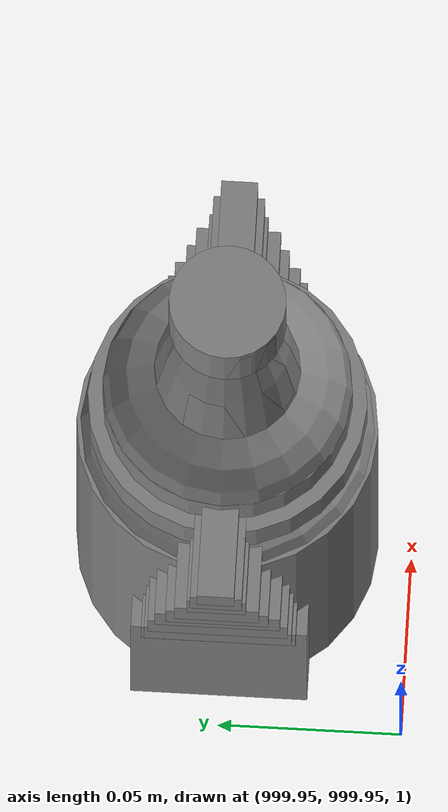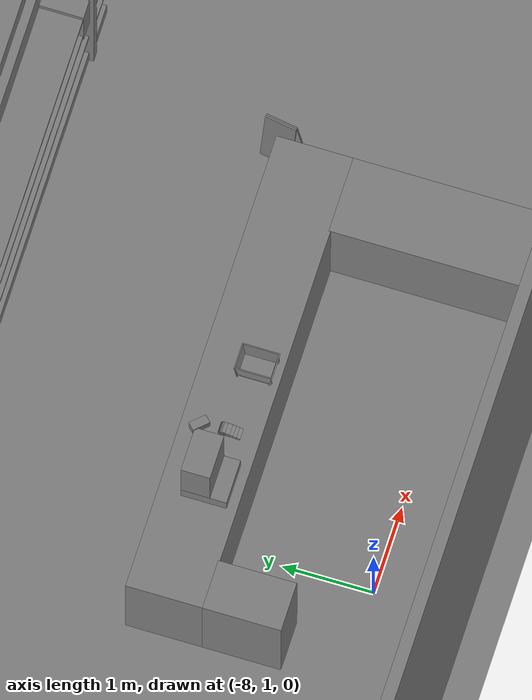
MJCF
<mujoco>
    <option gravity="0.000000000 0.000000000 -9.810000420" timestep="0.0166666" integrator="implicitfast" density="1.225" viscosity="1.8000001e-05" noslip_iterations="10" iterations="100" sdf_iterations="50">
        <flag multiccd="disable"/>
    </option>
    <size memory="1000M"/>
    <compiler coordinate="local"/>
    <worldbody>
        <light cutoff="30" pos="0 1 1" dir="0 -1 -2"/>
        <light cutoff="30" pos="0 -1 1" dir="0 1 -2"/>
        <body pos="-7.168000221 2.823999882 1.227496982" euler="-0.283413976 0.056829724 -0.133293271" name="openloong_gripper_2f85_fix_base_usda_Pos">
            <geom contype="1" conaffinity="1" density="1000" type="box" material="" rgba="0.500000000 0.500000000 0.500000000 1.000000000" solimp="0.899999976 0.949999988 0.001000000" friction="1.000000000 0.005000000 0.000100000" solref="0.020000000 1.000000000" margin="0" condim="3" group="0" pos="-0.002278805 0.074524641 -0.004134059" quat="0.315989345 0.948763072 -0.000000000 0.000000000" size="0.059999999 0.013000000 0.035000000" name="openloong_gripper_2f85_fix_base_usda_geom_B81F25DE_8E89_42C0_BB9C_C41981A8C58F"/>
            <geom contype="1" conaffinity="1" density="1000" type="box" material="" rgba="0.500000000 0.500000000 0.500000000 1.000000000" solimp="0.899999976 0.949999988 0.001000000" friction="1.000000000 0.005000000 0.000100000" solref="0.020000000 1.000000000" margin="0" condim="3" group="0" pos="-0.002278805 0.078031301 0.008128285" quat="0.990447521 -0.137893379 -0.000000000 -0.000000000" size="0.059999999 0.010000000 0.035000000" name="openloong_gripper_2f85_fix_base_usda_geom_98820BEB_6E42_4421_B953_BFA1C4939616"/>
            <geom contype="1" conaffinity="1" density="1000" type="box" material="" rgba="0.500000000 0.500000000 0.500000000 1.000000000" solimp="0.899999976 0.949999988 0.001000000" friction="1.000000000 0.005000000 0.000100000" solref="0.020000000 1.000000000" margin="0" condim="3" group="0" pos="-0.002278805 0.080785275 -0.002596974" quat="0.287325472 -0.957833409 0.000000000 -0.000000000" size="0.059999999 0.013000000 0.035000000" name="openloong_gripper_2f85_fix_base_usda_geom_FBE307A0_8238_48E1_BB80_56DC87D1D2F8"/>
            <geom contype="1" conaffinity="1" density="1000" type="box" material="" rgba="0.500000000 0.500000000 0.500000000 1.000000000" solimp="0.899999976 0.949999988 0.001000000" friction="1.000000000 0.005000000 0.000100000" solref="0.020000000 1.000000000" margin="0" condim="3" group="0" pos="-0.002278805 -0.098804474 -0.020146966" quat="0.988851666 0.148906454 0.000000000 -0.000000000" size="0.059999999 0.022000000 0.020000000" name="openloong_gripper_2f85_fix_base_usda_geom_54716D84_6E2C_4B8F_A737_C8B4A17EBC7C"/>
            <geom contype="1" conaffinity="1" density="1000" type="box" material="" rgba="0.500000000 0.500000000 0.500000000 1.000000000" solimp="0.899999976 0.949999988 0.001000000" friction="1.000000000 0.005000000 0.000100000" solref="0.020000000 1.000000000" margin="0" condim="3" group="0" pos="-0.002279282 0.019920111 0.012102962" quat="0.995421767 0.095583342 -0.000000000 -0.000000000" size="0.059999999 0.025000000 0.026000001" name="openloong_gripper_2f85_fix_base_usda_geom_6ECAE9BD_0611_4AD6_B577_80F444B31AE4"/>
            <geom contype="1" conaffinity="1" density="1000" type="box" material="" rgba="0.500000000 0.500000000 0.500000000 1.000000000" solimp="0.899999976 0.949999988 0.001000000" friction="1.000000000 0.005000000 0.000100000" solref="0.020000000 1.000000000" margin="0" condim="3" group="0" pos="-0.002279282 0.005734444 -0.014276862" quat="0.999571741 -0.029275302 -0.000000000 -0.000000000" size="0.059999999 0.050000001 0.010000000" name="openloong_gripper_2f85_fix_base_usda_geom_41D4DCE2_AE91_4238_AEDF_0F947D453776"/>
            <geom contype="1" conaffinity="1" density="1000" type="box" material="" rgba="0.500000000 0.500000000 0.500000000 1.000000000" solimp="0.899999976 0.949999988 0.001000000" friction="1.000000000 0.005000000 0.000100000" solref="0.020000000 1.000000000" margin="0" condim="3" group="0" pos="-0.002278805 0.079460382 0.007771969" quat="0.922590554 -0.385781586 0.000000000 -0.000000000" size="0.059999999 0.010000000 0.035000000" name="openloong_gripper_2f85_fix_base_usda_geom_B547DFC7_ADE1_457A_B1B7_7A25B4016EB6"/>
            <geom contype="1" conaffinity="1" density="1000" type="box" material="" rgba="0.500000000 0.500000000 0.500000000 1.000000000" solimp="0.899999976 0.949999988 0.001000000" friction="1.000000000 0.005000000 0.000100000" solref="0.020000000 1.000000000" margin="0" condim="3" group="0" pos="-0.002279282 0.081384182 -0.001320124" quat="0.590483785 -0.807049930 0.000000000 -0.000000000" size="0.059999999 0.013000000 0.035000000" name="openloong_gripper_2f85_fix_base_usda_geom_D9EAD479_1504_4401_87A3_E3DA04061E74"/>
            <geom contype="1" conaffinity="1" density="1000" type="box" material="" rgba="0.500000000 0.500000000 0.500000000 1.000000000" solimp="0.899999976 0.949999988 0.001000000" friction="1.000000000 0.005000000 0.000100000" solref="0.020000000 1.000000000" margin="0" condim="3" group="0" pos="-0.002278805 -0.059297800 -0.007972836" quat="0.988851666 0.148906454 0.000000000 -0.000000000" size="0.059999999 0.020000000 0.022000000" name="openloong_gripper_2f85_fix_base_usda_geom_6A58AA90_5A1D_4572_9BDC_B9EAE6B12986"/>
            <geom contype="1" conaffinity="1" density="1000" type="box" material="" rgba="0.500000000 0.500000000 0.500000000 1.000000000" solimp="0.899999976 0.949999988 0.001000000" friction="1.000000000 0.005000000 0.000100000" solref="0.020000000 1.000000000" margin="0" condim="3" group="0" pos="-0.002278805 0.076618671 -0.004656792" quat="0.004634961 0.999989629 -0.000000000 0.000000000" size="0.059999999 0.013000000 0.035000000" name="openloong_gripper_2f85_fix_base_usda_geom_74327FCC_960D_4CDC_A9B6_85EA42FF1FF1"/>
            <geom contype="1" conaffinity="1" density="1000" type="box" material="" rgba="0.500000000 0.500000000 0.500000000 1.000000000" solimp="0.899999976 0.949999988 0.001000000" friction="1.000000000 0.005000000 0.000100000" solref="0.020000000 1.000000000" margin="0" condim="3" group="0" pos="-0.002279282 -0.021952629 0.002960086" quat="0.991270423 0.131847665 -0.000000000 0.000000000" size="0.059999999 0.020000000 0.024000000" name="openloong_gripper_2f85_fix_base_usda_geom_99D10279_0FA0_4B20_97CB_727E570372E7"/>
            <geom contype="1" conaffinity="1" density="1000" type="box" material="" rgba="0.500000000 0.500000000 0.500000000 1.000000000" solimp="0.899999976 0.949999988 0.001000000" friction="1.000000000 0.005000000 0.000100000" solref="0.020000000 1.000000000" margin="0" condim="3" group="0" pos="-0.002278805 0.081418991 0.002587914" quat="0.803492308 -0.595315695 0.000000000 -0.000000000" size="0.059999999 0.013000000 0.035000000" name="openloong_gripper_2f85_fix_base_usda_geom_00C1EACA_47C8_455C_854A_AC00B3BCE85D"/>
            <geom contype="1" conaffinity="1" density="1000" type="box" material="" rgba="0.500000000 0.500000000 0.500000000 1.000000000" solimp="0.899999976 0.949999988 0.001000000" friction="1.000000000 0.005000000 0.000100000" solref="0.020000000 1.000000000" margin="0" condim="3" group="0" pos="-0.002278805 0.061115503 0.008545756" quat="0.999326169 0.036714450 0.000000000 -0.000000000" size="0.059999999 0.020000000 0.035000000" name="openloong_gripper_2f85_fix_base_usda_geom_4E7357E6_32BF_4F51_937F_3DC4E2E022BA"/>
            <freejoint name="openloong_gripper_2f85_fix_base_usda_pos_scan"/>
        </body>
        <body pos="-1.861002803 6.453862667 1.742253780" euler="93.006187439 24.740116119 151.526779175" mocap="true" name="spotlight6_SpotLight"/>
        <body pos="1000.000000000 1000.000000000 1.000000000" euler="0.000000000 0.000000000 0.000000000" name="openloong_gripper_2f85_fix_base_usda_jar_01">
            <geom contype="1" conaffinity="1" density="1000" type="box" material="" rgba="0.500000000 0.500000000 0.500000000 1.000000000" solimp="0.899999976 0.949999988 0.001000000" friction="1.000000000 0.005000000 0.000100000" solref="0.020000000 1.000000000" margin="0" condim="3" group="0" pos="0.000000000 0.000000000 0.006158113" quat="1.000000000 0.000000000 0.000000000 0.000000000" size="0.020000000 0.020000000 0.005000000" name="openloong_gripper_2f85_fix_base_usda_geom_F465CA99_1DE0_4EB3_97B3_626A25A43378"/>
            <geom contype="1" conaffinity="1" density="1000" type="cylinder" material="" rgba="0.500000000 0.500000000 0.500000000 1.000000000" solimp="0.899999976 0.949999988 0.001000000" friction="1.000000000 0.005000000 0.000100000" solref="0.020000000 1.000000000" margin="0" condim="3" group="0" pos="0.000000000 0.000000000 0.062744498" quat="1.000000000 0.000000000 0.000000000 0.000000000" size="0.041000001 0.052999999 1.000000000" name="openloong_gripper_2f85_fix_base_usda_geom_6FA97279_233B_47AE_A324_7263BF6955E4"/>
            <geom contype="1" conaffinity="1" density="1000" type="ellipsoid" material="" rgba="0.500000000 0.500000000 0.500000000 1.000000000" solimp="0.899999976 0.949999988 0.001000000" friction="1.000000000 0.005000000 0.000100000" solref="0.020000000 1.000000000" margin="0" condim="3" group="0" pos="0.000000000 0.000000000 0.122252703" quat="1.000000000 0.000000000 0.000000000 0.000000000" size="0.035999998 0.035999998 0.010000000" name="openloong_gripper_2f85_fix_base_usda_geom_761B3D58_EDAE_486C_89A7_DC5715C8379A"/>
            <geom contype="1" conaffinity="1" density="1000" type="cylinder" material="" rgba="0.500000000 0.500000000 0.500000000 1.000000000" solimp="0.899999976 0.949999988 0.001000000" friction="1.000000000 0.005000000 0.000100000" solref="0.020000000 1.000000000" margin="0" condim="3" group="0" pos="0.000000000 0.000000000 0.015747190" quat="1.000000000 0.000000000 0.000000000 0.000000000" size="0.035000000 0.010000000 1.000000000" name="openloong_gripper_2f85_fix_base_usda_geom_84B2FA54_D9FD_4AB5_B77D_81407DC8D7C4"/>
            <geom contype="1" conaffinity="1" density="1000" type="ellipsoid" material="" rgba="0.500000000 0.500000000 0.500000000 1.000000000" solimp="0.899999976 0.949999988 0.001000000" friction="1.000000000 0.005000000 0.000100000" solref="0.020000000 1.000000000" margin="0" condim="3" group="0" pos="0.000000000 0.000000000 0.115815401" quat="1.000000000 0.000000000 0.000000000 0.000000000" size="0.039999999 0.039999999 0.010000000" name="openloong_gripper_2f85_fix_base_usda_geom_E0F84630_9C59_46C1_9270_50E886B93D13"/>
            <geom contype="1" conaffinity="1" density="1000" type="cylinder" material="" rgba="0.500000000 0.500000000 0.500000000 1.000000000" solimp="0.899999976 0.949999988 0.001000000" friction="1.000000000 0.005000000 0.000100000" solref="0.020000000 1.000000000" margin="0" condim="3" group="0" pos="0.000000000 0.000000000 0.133183479" quat="1.000000000 0.000000000 0.000000000 0.000000000" size="0.037999999 0.006500000 1.000000000" name="openloong_gripper_2f85_fix_base_usda_geom_43AA31D8_831D_4E4B_B5E6_4B31D7788C01"/>
            <freejoint name="openloong_gripper_2f85_fix_base_usda_jar_01_joint"/>
            <site size="0.005000000 0.005000000 0.005000000" rgba="0.500000000 0.500000000 0.500000000 1.000000000" pos="0.000000000 0.000000000 0.000000000" quat="1.000000000 0.000000000 0.000000000 0.000000000" group="0" type="sphere" name="openloong_gripper_2f85_fix_base_usda_jar_01site"/>
        </body>
        <body pos="1000.000000000 1000.000000000 1.000000000" euler="0.000000000 0.000000000 0.000000000" name="openloong_gripper_2f85_fix_base_usda_bottle_blue">
            <geom contype="1" conaffinity="1" density="1000" type="ellipsoid" material="" rgba="0.500000000 0.500000000 0.500000000 1.000000000" solimp="0.899999976 0.949999988 0.001000000" friction="1.000000000 0.005000000 0.000100000" solref="0.020000000 1.000000000" margin="0" condim="3" group="0" pos="0.000000000 0.000000000 0.118920922" quat="1.000000000 0.000000000 0.000000000 0.000000000" size="0.030999999 0.030999999 0.029999999" name="openloong_gripper_2f85_fix_base_usda_geom_50A827FD_6ACC_43D8_9921_7E2E56E07F85"/>
            <geom contype="1" conaffinity="1" density="1000" type="box" material="" rgba="0.500000000 0.500000000 0.500000000 1.000000000" solimp="0.899999976 0.949999988 0.001000000" friction="1.000000000 0.005000000 0.000100000" solref="0.020000000 1.000000000" margin="0" condim="3" group="0" pos="0.000000000 0.000000000 0.002164602" quat="1.000000000 0.000000000 0.000000000 0.000000000" size="0.020000000 0.020000000 0.003000000" name="openloong_gripper_2f85_fix_base_usda_geom_D371613B_7BFF_44FB_9D4E_721EB91B6F04"/>
            <geom contype="1" conaffinity="1" density="1000" type="cylinder" material="" rgba="0.500000000 0.500000000 0.500000000 1.000000000" solimp="0.899999976 0.949999988 0.001000000" friction="1.000000000 0.005000000 0.000100000" solref="0.020000000 1.000000000" margin="0" condim="3" group="0" pos="0.000000000 -0.000366211 0.060859680" quat="1.000000000 0.000000000 0.000000000 0.000000000" size="0.030999999 0.057999998 1.000000000" name="openloong_gripper_2f85_fix_base_usda_geom_459D4947_65ED_4426_B925_635C4C179B82"/>
            <geom contype="1" conaffinity="1" density="1000" type="cylinder" material="" rgba="0.500000000 0.500000000 0.500000000 1.000000000" solimp="0.899999976 0.949999988 0.001000000" friction="1.000000000 0.005000000 0.000100000" solref="0.020000000 1.000000000" margin="0" condim="3" group="0" pos="0.000000000 0.000000000 0.220594406" quat="1.000000000 0.000000000 0.000000000 0.000000000" size="0.016000001 0.010000000 1.000000000" name="openloong_gripper_2f85_fix_base_usda_geom_8BD87371_1A3D_4F01_A7E3_D537A24801F1"/>
            <geom contype="1" conaffinity="1" density="1000" type="ellipsoid" material="" rgba="0.500000000 0.500000000 0.500000000 1.000000000" solimp="0.899999976 0.949999988 0.001000000" friction="1.000000000 0.005000000 0.000100000" solref="0.020000000 1.000000000" margin="0" condim="3" group="0" pos="0.000000000 0.000000000 0.144259930" quat="1.000000000 0.000000000 0.000000000 0.000000000" size="0.021000000 0.021000000 0.079999998" name="openloong_gripper_2f85_fix_base_usda_geom_651A83E2_84D2_4938_B99C_FA5CDF390827"/>
            <freejoint name="openloong_gripper_2f85_fix_base_usda_bottle_blue_joint"/>
            <site size="0.005000000 0.005000000 0.005000000" rgba="0.500000000 0.500000000 0.500000000 1.000000000" pos="0.000000000 0.000000000 0.000000000" quat="0.999961913 0.008726535 0.000000000 0.000000000" group="0" type="sphere" name="openloong_gripper_2f85_fix_base_usda_bottle_bluesite"/>
        </body>
        <body pos="1000.000000000 1000.000000000 1.000000000" euler="0.000000000 0.000000000 0.000000000" name="openloong_gripper_2f85_fix_base_usda_can">
            <geom contype="1" conaffinity="1" density="1000" type="cylinder" material="" rgba="0.500000000 0.500000000 0.500000000 1.000000000" solimp="0.899999976 0.949999988 0.001000000" friction="1.000000000 0.005000000 0.000100000" solref="0.020000000 1.000000000" margin="0" condim="3" group="0" pos="0.000000000 0.000000000 0.079676986" quat="1.000000000 0.000000000 0.000000000 0.000000000" size="0.034000002 0.071999997 1.000000000" name="openloong_gripper_2f85_fix_base_usda_geom_B29BBEEB_C0E9_45E5_A76B_9E1D68706891"/>
            <geom contype="1" conaffinity="1" density="1000" type="ellipsoid" material="" rgba="0.500000000 0.500000000 0.500000000 1.000000000" solimp="0.899999976 0.949999988 0.001000000" friction="1.000000000 0.005000000 0.000100000" solref="0.020000000 1.000000000" margin="0" condim="3" group="0" pos="0.000000000 0.000000000 0.151854277" quat="1.000000000 0.000000000 0.000000000 0.000000000" size="0.034000002 0.034000002 0.020000000" name="openloong_gripper_2f85_fix_base_usda_geom_E34EE73A_DB70_4D15_9313_891D62C66985"/>
            <geom contype="1" conaffinity="1" density="1000" type="box" material="" rgba="0.500000000 0.500000000 0.500000000 1.000000000" solimp="0.899999976 0.949999988 0.001000000" friction="1.000000000 0.005000000 0.000100000" solref="0.020000000 1.000000000" margin="0" condim="3" group="0" pos="0.000000000 0.000000000 0.004777670" quat="1.000000000 0.000000000 0.000000000 0.000000000" size="0.020000000 0.020000000 0.005000000" name="openloong_gripper_2f85_fix_base_usda_geom_FEE1E693_A1CA_4C4D_9271_BAF6CEC24331"/>
            <freejoint name="openloong_gripper_2f85_fix_base_usda_can_joint"/>
            <site size="0.005000000 0.005000000 0.005000000" rgba="0.500000000 0.500000000 0.500000000 1.000000000" pos="0.000000000 0.000000000 0.000000000" quat="1.000000000 0.000000000 0.000000000 0.000000000" group="0" type="sphere" name="openloong_gripper_2f85_fix_base_usda_cansite"/>
        </body>
        <body pos="1000.000000000 1000.000000000 1.000000000" euler="0.000000000 0.000000000 0.000000000" name="openloong_gripper_2f85_fix_base_usda_bottle_red">
            <geom contype="1" conaffinity="1" density="1000" type="ellipsoid" material="" rgba="0.500000000 0.500000000 0.500000000 1.000000000" solimp="0.899999976 0.949999988 0.001000000" friction="1.000000000 0.005000000 0.000100000" solref="0.020000000 1.000000000" margin="0" condim="3" group="0" pos="0.000000000 0.000000000 0.144284487" quat="1.000000000 0.000000000 0.000000000 0.000000000" size="0.021000000 0.021000000 0.079999998" name="openloong_gripper_2f85_fix_base_usda_geom_E40834B3_5E44_459F_879F_BB768F7B64B2"/>
            <geom contype="1" conaffinity="1" density="1000" type="cylinder" material="" rgba="0.500000000 0.500000000 0.500000000 1.000000000" solimp="0.899999976 0.949999988 0.001000000" friction="1.000000000 0.005000000 0.000100000" solref="0.020000000 1.000000000" margin="0" condim="3" group="0" pos="0.000000000 0.000000000 0.220618963" quat="1.000000000 0.000000000 0.000000000 0.000000000" size="0.016000001 0.010000000 1.000000000" name="openloong_gripper_2f85_fix_base_usda_geom_B715348F_2790_4F5D_AA9E_C7B752C5E9F2"/>
            <geom contype="1" conaffinity="1" density="1000" type="ellipsoid" material="" rgba="0.500000000 0.500000000 0.500000000 1.000000000" solimp="0.899999976 0.949999988 0.001000000" friction="1.000000000 0.005000000 0.000100000" solref="0.020000000 1.000000000" margin="0" condim="3" group="0" pos="0.000000000 0.000000000 0.118945479" quat="1.000000000 0.000000000 0.000000000 0.000000000" size="0.030999999 0.030999999 0.029999999" name="openloong_gripper_2f85_fix_base_usda_geom_1395B159_E208_46E4_B616_C76A33A0EA44"/>
            <geom contype="1" conaffinity="1" density="1000" type="box" material="" rgba="0.500000000 0.500000000 0.500000000 1.000000000" solimp="0.899999976 0.949999988 0.001000000" friction="1.000000000 0.005000000 0.000100000" solref="0.020000000 1.000000000" margin="0" condim="3" group="0" pos="0.000000000 0.000000000 0.002189159" quat="1.000000000 0.000000000 0.000000000 0.000000000" size="0.020000000 0.020000000 0.003000000" name="openloong_gripper_2f85_fix_base_usda_geom_E2304F00_7B08_420C_9436_1982293916C2"/>
            <geom contype="1" conaffinity="1" density="1000" type="cylinder" material="" rgba="0.500000000 0.500000000 0.500000000 1.000000000" solimp="0.899999976 0.949999988 0.001000000" friction="1.000000000 0.005000000 0.000100000" solref="0.020000000 1.000000000" margin="0" condim="3" group="0" pos="0.000000000 -0.000366211 0.060884237" quat="1.000000000 0.000000000 0.000000000 0.000000000" size="0.030999999 0.057999998 1.000000000" name="openloong_gripper_2f85_fix_base_usda_geom_5F829EC7_69CC_4C75_8A5D_C6BB8F5ECBAC"/>
            <freejoint name="openloong_gripper_2f85_fix_base_usda_bottle_red_joint"/>
            <site size="0.005000000 0.005000000 0.005000000" rgba="0.500000000 0.500000000 0.500000000 1.000000000" pos="0.000000000 0.000000000 0.000000000" quat="0.999961913 0.008726535 0.000000000 0.000000000" group="0" type="sphere" name="openloong_gripper_2f85_fix_base_usda_bottle_redsite"/>
        </body>
        <body pos="-1.852025986 5.738976002 1.669286609" euler="123.444389343 -7.586629868 134.551925659" mocap="true" name="spotlight4_SpotLight"/>
        <body pos="1000.000000000 1000.000000000 1.000000000" euler="0.000000000 0.000000000 0.000000000" name="openloong_gripper_2f85_fix_base_usda_salt">
            <geom contype="1" conaffinity="1" density="1000" type="box" material="" rgba="0.500000000 0.500000000 0.500000000 1.000000000" solimp="0.899999976 0.949999988 0.001000000" friction="1.000000000 0.005000000 0.000100000" solref="0.020000000 1.000000000" margin="0" condim="3" group="0" pos="0.000305176 0.000000000 0.084862232" quat="1.000000000 0.000000000 0.000000000 0.000000000" size="0.048999999 0.018999999 0.005000000" name="openloong_gripper_2f85_fix_base_usda_geom_A17C6CD3_0C39_4490_B05E_B8506A95B901"/>
            <geom contype="1" conaffinity="1" density="1000" type="box" material="" rgba="0.500000000 0.500000000 0.500000000 1.000000000" solimp="0.899999976 0.949999988 0.001000000" friction="1.000000000 0.005000000 0.000100000" solref="0.020000000 1.000000000" margin="0" condim="3" group="0" pos="0.000305176 0.000000000 0.104564309" quat="1.000000000 0.000000000 0.000000000 0.000000000" size="0.052000001 0.014000000 0.005000000" name="openloong_gripper_2f85_fix_base_usda_geom_AFB03BDD_AF19_4CB0_A187_40E008D8E203"/>
            <geom contype="1" conaffinity="1" density="1000" type="box" material="" rgba="0.500000000 0.500000000 0.500000000 1.000000000" solimp="0.899999976 0.949999988 0.001000000" friction="1.000000000 0.005000000 0.000100000" solref="0.020000000 1.000000000" margin="0" condim="3" group="0" pos="0.000305176 0.000000000 0.114487171" quat="1.000000000 0.000000000 0.000000000 0.000000000" size="0.054000001 0.011500000 0.005000000" name="openloong_gripper_2f85_fix_base_usda_geom_01E6D930_8CF6_44A7_A195_DCCE48994380"/>
            <geom contype="1" conaffinity="1" density="1000" type="box" material="" rgba="0.500000000 0.500000000 0.500000000 1.000000000" solimp="0.899999976 0.949999988 0.001000000" friction="1.000000000 0.005000000 0.000100000" solref="0.020000000 1.000000000" margin="0" condim="3" group="0" pos="0.000305176 0.000000000 0.075103164" quat="1.000000000 0.000000000 0.000000000 0.000000000" size="0.048000000 0.020000000 0.005000000" name="openloong_gripper_2f85_fix_base_usda_geom_F9418347_7740_4708_9B18_B93AB7DCC354"/>
            <geom contype="1" conaffinity="1" density="1000" type="box" material="" rgba="0.500000000 0.500000000 0.500000000 1.000000000" solimp="0.899999976 0.949999988 0.001000000" friction="1.000000000 0.005000000 0.000100000" solref="0.020000000 1.000000000" margin="0" condim="3" group="0" pos="0.000305176 0.000000000 0.134892464" quat="1.000000000 0.000000000 0.000000000 0.000000000" size="0.057000000 0.007000000 0.005000000" name="openloong_gripper_2f85_fix_base_usda_geom_5A52F1E3_DFA8_4AAF_BC95_F29B1C7562BD"/>
            <geom contype="1" conaffinity="1" density="1000" type="box" material="" rgba="0.500000000 0.500000000 0.500000000 1.000000000" solimp="0.899999976 0.949999988 0.001000000" friction="1.000000000 0.005000000 0.000100000" solref="0.020000000 1.000000000" margin="0" condim="3" group="0" pos="0.000305176 0.000000000 0.094920278" quat="1.000000000 0.000000000 0.000000000 0.000000000" size="0.050000001 0.017000001 0.005000000" name="openloong_gripper_2f85_fix_base_usda_geom_FDD6046A_88CD_4E2C_803D_CBF5BE0872F8"/>
            <geom contype="1" conaffinity="1" density="1000" type="box" material="" rgba="0.500000000 0.500000000 0.500000000 1.000000000" solimp="0.899999976 0.949999988 0.001000000" friction="1.000000000 0.005000000 0.000100000" solref="0.020000000 1.000000000" margin="0" condim="3" group="0" pos="0.000305176 0.000000000 0.065204859" quat="1.000000000 0.000000000 0.000000000 0.000000000" size="0.045000002 0.021000000 0.005000000" name="openloong_gripper_2f85_fix_base_usda_geom_EB5A40B0_734D_4F04_97C7_F42919BA715B"/>
            <geom contype="1" conaffinity="1" density="1000" type="box" material="" rgba="0.500000000 0.500000000 0.500000000 1.000000000" solimp="0.899999976 0.949999988 0.001000000" friction="1.000000000 0.005000000 0.000100000" solref="0.020000000 1.000000000" margin="0" condim="3" group="0" pos="0.000305176 0.000000000 0.144135714" quat="1.000000000 0.000000000 0.000000000 0.000000000" size="0.059000000 0.005000000 0.004000000" name="openloong_gripper_2f85_fix_base_usda_geom_63E91A78_1D07_4EF4_A528_C871A81F0162"/>
            <geom contype="1" conaffinity="1" density="1000" type="box" material="" rgba="0.500000000 0.500000000 0.500000000 1.000000000" solimp="0.899999976 0.949999988 0.001000000" friction="1.000000000 0.005000000 0.000100000" solref="0.020000000 1.000000000" margin="0" condim="3" group="0" pos="0.000000000 0.000000000 0.031593561" quat="1.000000000 0.000000000 0.000000000 0.000000000" size="0.041999999 0.024000000 0.029999999" name="openloong_gripper_2f85_fix_base_usda_geom_397F5BA2_312C_4148_BFE4_53413E899354"/>
            <geom contype="1" conaffinity="1" density="1000" type="box" material="" rgba="0.500000000 0.500000000 0.500000000 1.000000000" solimp="0.899999976 0.949999988 0.001000000" friction="1.000000000 0.005000000 0.000100000" solref="0.020000000 1.000000000" margin="0" condim="3" group="0" pos="0.000305176 0.000000000 0.124608755" quat="1.000000000 0.000000000 0.000000000 0.000000000" size="0.055000000 0.008000000 0.005000000" name="openloong_gripper_2f85_fix_base_usda_geom_B1849042_9376_43CF_B648_DC86CCACACDA"/>
            <freejoint name="openloong_gripper_2f85_fix_base_usda_salt_joint"/>
            <site size="0.005000000 0.005000000 0.005000000" rgba="0.500000000 0.500000000 0.500000000 1.000000000" pos="0.000000000 0.000000000 0.000000000" quat="1.000000000 0.000000000 0.000000000 0.000000000" group="0" type="sphere" name="openloong_gripper_2f85_fix_base_usda_saltsite"/>
        </body>
        <body pos="-2.052596807 6.470633984 1.804753780" euler="82.404136658 -78.210632324 94.578598022" mocap="true" name="spotlight3_SpotLight"/>
        <body pos="0.000000000 0.000000000 0.000000000" euler="0.000000000 0.000000000 0.000000000" name="Interactive Objects_Interactive Objects"/>
        <body pos="0.000000000 0.000000000 0.000000000" euler="0.000000000 0.000000000 0.000000000" name=" Static Objects_ Static Objects">
            <geom contype="1" conaffinity="1" density="1000" type="box" material="" rgba="0.500000000 0.500000000 0.500000000 1.000000000" solimp="0.899999976 0.949999988 0.001000000" friction="1.000000000 0.005000000 0.000100000" solref="0.020000000 1.000000000" margin="0" condim="3" group="0" pos="-6.286010742 6.153595448 1.563861728" quat="0.707107067 0.000000000 0.000000000 0.707106471" size="0.529999971 3.134999990 0.025000000" name=" Static Objects_geom_260776ED_C079_41CD_B9F3_A03826781C90"/>
            <geom contype="1" conaffinity="1" density="1000" type="box" material="" rgba="0.500000000 0.500000000 0.500000000 1.000000000" solimp="0.899999976 0.949999988 0.001000000" friction="1.000000000 0.005000000 0.000100000" solref="0.020000000 1.000000000" margin="0" condim="3" group="0" pos="-3.101639986 6.150595188 1.018643856" quat="1.000000000 0.000000000 0.000000000 0.000000000" size="0.050000001 0.579999983 1.019999981" name=" Static Objects_geom_FDDD67CF_B4FF_452B_B216_3A61C178D1D8"/>
            <geom contype="1" conaffinity="1" density="1000" type="box" material="" rgba="0.500000000 0.500000000 0.500000000 1.000000000" solimp="0.899999976 0.949999988 0.001000000" friction="1.000000000 0.005000000 0.000100000" solref="0.020000000 1.000000000" margin="0" condim="3" group="0" pos="-2.825197220 6.153595448 1.563861728" quat="0.707107067 0.000000000 0.000000000 0.707106471" size="0.550000012 0.239999995 0.025000000" name=" Static Objects_geom_E9F243D0_7165_4F5E_B846_892C59944128"/>
            <geom contype="1" conaffinity="1" density="1000" type="box" material="" rgba="0.500000000 0.500000000 0.500000000 1.000000000" solimp="0.899999976 0.949999988 0.001000000" friction="1.000000000 0.005000000 0.000100000" solref="0.020000000 1.000000000" margin="0" condim="3" group="0" pos="-6.311686516 6.153595448 1.018643856" quat="0.707107067 0.000000000 0.000000000 0.707106471" size="0.050000001 3.150000095 1.019999981" name=" Static Objects_geom_F83F4CE8_E741_4DE7_ADA0_76DE2909186A"/>
            <geom contype="1" conaffinity="1" density="1000" type="box" material="" rgba="0.500000000 0.500000000 0.500000000 1.000000000" solimp="0.899999976 0.949999988 0.001000000" friction="1.000000000 0.005000000 0.000100000" solref="0.020000000 1.000000000" margin="0" condim="3" group="0" pos="-2.825197220 6.153595448 1.115278244" quat="0.707107067 0.000000000 0.000000000 0.707106471" size="0.550000012 0.239999995 0.025000000" name=" Static Objects_geom_32B60FCB_50B0_4CE5_9890_A22EB88C0B09"/>
            <geom contype="1" conaffinity="1" density="1000" type="box" material="" rgba="0.500000000 0.500000000 0.500000000 1.000000000" solimp="0.899999976 0.949999988 0.001000000" friction="1.000000000 0.005000000 0.000100000" solref="0.020000000 1.000000000" margin="0" condim="3" group="0" pos="-6.293097973 6.153595448 1.114443064" quat="0.707107067 0.000000000 0.000000000 0.707106471" size="0.529999971 3.134999990 0.025000000" name=" Static Objects_geom_B4DE25C4_7FCB_498F_8F45_368E3339CF38"/>
            <geom contype="1" conaffinity="1" density="1000" type="box" material="" rgba="0.500000000 0.500000000 0.500000000 1.000000000" solimp="0.899999976 0.949999988 0.001000000" friction="1.000000000 0.005000000 0.000100000" solref="0.020000000 1.000000000" margin="0" condim="3" group="0" pos="-2.825197220 6.153595448 0.629031777" quat="0.707107067 0.000000000 0.000000000 0.707106471" size="0.550000012 0.239999995 0.025000000" name=" Static Objects_geom_79D1F9E3_7A5F_41F0_A047_24DF3D14E447"/>
            <geom contype="1" conaffinity="1" density="1000" type="box" material="" rgba="0.500000000 0.500000000 0.500000000 1.000000000" solimp="0.899999976 0.949999988 0.001000000" friction="1.000000000 0.005000000 0.000100000" solref="0.020000000 1.000000000" margin="0" condim="3" group="0" pos="-6.286010742 6.153595448 0.096129179" quat="0.707107067 0.000000000 0.000000000 0.707106471" size="0.529999971 3.134999990 0.098999999" name=" Static Objects_geom_C52E05F6_6414_4AE5_B743_CB4F19AADA56"/>
            <geom contype="1" conaffinity="1" density="1000" type="box" material="" rgba="0.500000000 0.500000000 0.500000000 1.000000000" solimp="0.899999976 0.949999988 0.001000000" friction="1.000000000 0.005000000 0.000100000" solref="0.020000000 1.000000000" margin="0" condim="3" group="0" pos="-2.825197220 6.153595448 0.097434282" quat="0.707107067 0.000000000 0.000000000 0.707106471" size="0.550000012 0.239999995 0.098999999" name=" Static Objects_geom_87F4AF50_9EA4_40EF_8128_4B4EBD886ED9"/>
            <geom contype="1" conaffinity="1" density="1000" type="box" material="" rgba="0.500000000 0.500000000 0.500000000 1.000000000" solimp="0.899999976 0.949999988 0.001000000" friction="1.000000000 0.005000000 0.000100000" solref="0.020000000 1.000000000" margin="0" condim="3" group="0" pos="-6.286010742 6.153595448 0.629031777" quat="0.707107067 0.000000000 0.000000000 0.707106471" size="0.529999971 3.134999990 0.025000000" name=" Static Objects_geom_2443E97D_9CD2_4281_9350_B1515F239E90"/>
            <geom contype="1" conaffinity="1" density="1000" type="box" material="" rgba="0.500000000 0.500000000 0.500000000 1.000000000" solimp="0.899999976 0.949999988 0.001000000" friction="1.000000000 0.005000000 0.000100000" solref="0.020000000 1.000000000" margin="0" condim="3" group="0" pos="-6.000000000 20.159999847 2.000000000" quat="1.000000000 0.000000000 0.000000000 0.000000000" size="6.079999924 0.070000000 2.000000000" name=" Static Objects_geom_9B4C66DD_90EE_41E0_8032_BC278B239316"/>
            <geom contype="1" conaffinity="1" density="1000" type="box" material="" rgba="0.500000000 0.500000000 0.500000000 1.000000000" solimp="0.899999976 0.949999988 0.001000000" friction="1.000000000 0.005000000 0.000100000" solref="0.020000000 1.000000000" margin="0" condim="3" group="0" pos="-6.000000000 0.035000000 2.000000000" quat="1.000000000 0.000000000 0.000000000 0.000000000" size="6.079999924 0.070000000 2.000000000" name=" Static Objects_geom_B2DFC572_1C23_4909_B1E2_8C72796785B2"/>
            <geom contype="1" conaffinity="1" density="1000" type="box" material="" rgba="0.500000000 0.500000000 0.500000000 1.000000000" solimp="0.899999976 0.949999988 0.001000000" friction="1.000000000 0.005000000 0.000100000" solref="0.020000000 1.000000000" margin="0" condim="3" group="0" pos="0.000000000 10.000000000 2.000000000" quat="1.000000000 0.000000000 0.000000000 0.000000000" size="0.070000000 10.500000000 2.000000000" name=" Static Objects_geom_C716FC93_5D32_4C8A_A8AE_06EC65CB4234"/>
            <geom contype="1" conaffinity="1" density="1000" type="box" material="" rgba="0.500000000 0.500000000 0.500000000 1.000000000" solimp="0.899999976 0.949999988 0.001000000" friction="1.000000000 0.005000000 0.000100000" solref="0.020000000 1.000000000" margin="0" condim="3" group="0" pos="-12.050000191 10.000000000 2.000000000" quat="1.000000000 0.000000000 0.000000000 0.000000000" size="0.070000000 10.500000000 2.000000000" name=" Static Objects_geom_133C35B9_7913_469F_8E12_FD64FB504F7E"/>
            <geom contype="1" conaffinity="1" density="1000" type="plane" material="" rgba="0.500000000 0.500000000 0.500000000 1.000000000" solimp="0.899999976 0.949999988 0.001000000" friction="1.000000000 0.005000000 0.000100000" solref="0.020000000 1.000000000" margin="0" condim="3" group="0" pos="-6.000000000 10.399999619 0.000000000" quat="1.000000000 0.000000000 0.000000000 0.000000000" size="6.050000191 10.800000191 0.010000000" name=" Static Objects_geom_F50C6545_D21F_499A_B3C0_547E6EA5F1C7"/>
            <geom contype="1" conaffinity="1" density="1000" type="box" material="" rgba="0.500000000 0.500000000 0.500000000 1.000000000" solimp="0.899999976 0.949999988 0.001000000" friction="1.000000000 0.005000000 0.000100000" solref="0.020000000 1.000000000" margin="0" condim="3" group="0" pos="-8.830721855 2.096410990 0.549305558" quat="1.000000000 0.000000000 0.000000000 0.000000000" size="0.280000001 0.430000007 0.550000012" name=" Static Objects_geom_0892607D_159C_4326_9F2D_239D77BC8EFB"/>
            <geom contype="1" conaffinity="1" density="1000" type="box" material="" rgba="0.500000000 0.500000000 0.500000000 1.000000000" solimp="0.899999976 0.949999988 0.001000000" friction="1.000000000 0.005000000 0.000100000" solref="0.020000000 1.000000000" margin="0" condim="3" group="0" pos="-6.460197449 2.937205315 0.548931718" quat="1.000000000 0.000000000 0.000000000 0.000000000" size="2.650000095 0.430000007 0.550000012" name=" Static Objects_geom_3CD14AE2_7264_4DD4_88E1_65E1BC9D81D3"/>
            <geom contype="1" conaffinity="1" density="1000" type="box" material="" rgba="0.500000000 0.500000000 0.500000000 1.000000000" solimp="0.899999976 0.949999988 0.001000000" friction="1.000000000 0.005000000 0.000100000" solref="0.020000000 1.000000000" margin="0" condim="3" group="0" pos="-4.240264893 1.327049494 0.549888909" quat="1.000000000 0.000000000 0.000000000 0.000000000" size="0.430000007 1.200000048 0.550000012" name=" Static Objects_geom_CBD779EC_B7D7_4443_9239_834605B7D5EE"/>
            <geom contype="1" conaffinity="1" density="1000" type="box" material="" rgba="0.500000000 0.500000000 0.500000000 1.000000000" solimp="0.899999976 0.949999988 0.001000000" friction="1.000000000 0.005000000 0.000100000" solref="0.020000000 1.000000000" margin="0" condim="3" group="0" pos="-7.408766270 3.088089943 1.776644945" quat="0.928051054 0.000000000 0.000000000 0.372453064" size="0.050000001 0.100000001 0.050000001" name=" Static Objects_geom_DA7A312B_1EDE_4F16_A8C6_1FCE61B98B1B"/>
            <geom contype="1" conaffinity="1" density="1000" type="box" material="" rgba="0.500000000 0.500000000 0.500000000 1.000000000" solimp="0.899999976 0.949999988 0.001000000" friction="1.000000000 0.005000000 0.000100000" solref="0.020000000 1.000000000" margin="0" condim="3" group="0" pos="-7.437745571 3.067511320 1.289965630" quat="1.000000000 0.000000000 0.000000000 0.000000000" size="0.029999999 0.020000000 0.020000000" name=" Static Objects_geom_74B16803_7D4E_4C3D_A91F_B34542F5869C"/>
            <geom contype="1" conaffinity="1" density="1000" type="box" material="" rgba="0.500000000 0.500000000 0.500000000 1.000000000" solimp="0.899999976 0.949999988 0.001000000" friction="1.000000000 0.005000000 0.000100000" solref="0.020000000 1.000000000" margin="0" condim="3" group="0" pos="-7.719123363 2.867671013 1.173410416" quat="1.000000000 0.000000000 0.000000000 0.000000000" size="0.250000000 0.250000000 0.079999998" name=" Static Objects_geom_5CB3B653_8242_4016_9570_C7E56208B8C9"/>
            <geom contype="1" conaffinity="1" density="1000" type="box" material="" rgba="0.500000000 0.500000000 0.500000000 1.000000000" solimp="0.899999976 0.949999988 0.001000000" friction="1.000000000 0.005000000 0.000100000" solref="0.020000000 1.000000000" margin="0" condim="3" group="0" pos="-7.719123363 2.958004713 1.530241251" quat="1.000000000 0.000000000 0.000000000 0.000000000" size="0.250000000 0.159999996 0.280000001" name=" Static Objects_geom_22AE5760_1F49_4F38_A6DC_4D0479B5D0D8"/>
            <geom contype="1" conaffinity="1" density="1000" type="cylinder" material="" rgba="0.500000000 0.500000000 0.500000000 1.000000000" solimp="0.899999976 0.949999988 0.001000000" friction="1.000000000 0.005000000 0.000100000" solref="0.020000000 1.000000000" margin="0" condim="3" group="0" pos="-7.427312374 3.069516420 1.502544641" quat="0.928051054 0.000000000 0.000000000 0.372453064" size="0.015000000 0.230000004 0.100000001" name=" Static Objects_geom_AE5F318A_C869_4870_B11F_40376881F492"/>
            <geom contype="1" conaffinity="1" density="1000" type="box" material="" rgba="0.500000000 0.500000000 0.500000000 1.000000000" solimp="0.899999976 0.949999988 0.001000000" friction="1.000000000 0.005000000 0.000100000" solref="0.020000000 1.000000000" margin="0" condim="3" group="0" pos="-9.058088303 6.434794426 1.209077358" quat="1.000000000 0.000000000 0.000000000 0.000000000" size="0.250000000 0.100000001 0.070000000" name=" Static Objects_geom_3273405D_E31F_45DF_B4B6_23930C448EEE"/>
            <geom contype="1" conaffinity="1" density="1000" type="box" material="" rgba="0.500000000 0.500000000 0.500000000 1.000000000" solimp="0.899999976 0.949999988 0.001000000" friction="1.000000000 0.005000000 0.000100000" solref="0.020000000 1.000000000" margin="0" condim="3" group="0" pos="-5.611940861 6.318420410 0.350975692" quat="1.000000000 0.000000000 0.000000000 0.000000000" size="0.699999988 0.100000001 0.150000006" name=" Static Objects_geom_99B42BB9_A500_4441_80C2_E38AAF2ABD3E"/>
            <geom contype="1" conaffinity="1" density="1000" type="box" material="" rgba="0.500000000 0.500000000 0.500000000 1.000000000" solimp="0.899999976 0.949999988 0.001000000" friction="1.000000000 0.005000000 0.000100000" solref="0.020000000 1.000000000" margin="0" condim="3" group="0" pos="-9.237723351 6.464855671 1.209077358" quat="1.000000000 0.000000000 0.000000000 0.000000000" size="0.100000001 0.100000001 0.070000000" name=" Static Objects_geom_4C9E5BEC_F020_4F21_B475_7646E502C977"/>
            <geom contype="1" conaffinity="1" density="1000" type="box" material="" rgba="0.500000000 0.500000000 0.500000000 1.000000000" solimp="0.899999976 0.949999988 0.001000000" friction="1.000000000 0.005000000 0.000100000" solref="0.020000000 1.000000000" margin="0" condim="3" group="0" pos="-6.300771236 6.459744930 1.744376063" quat="1.000000000 0.000000000 0.000000000 0.000000000" size="3.000000000 0.200000003 0.150000006" name=" Static Objects_geom_15EE9AE9_6AD4_4A5B_B662_E877826FB2B9"/>
            <geom contype="1" conaffinity="1" density="1000" type="box" material="" rgba="0.500000000 0.500000000 0.500000000 1.000000000" solimp="0.899999976 0.949999988 0.001000000" friction="1.000000000 0.005000000 0.000100000" solref="0.020000000 1.000000000" margin="0" condim="3" group="0" pos="-7.373087406 6.458900928 1.214329123" quat="1.000000000 0.000000000 0.000000000 0.000000000" size="0.250000000 0.200000003 0.075000003" name=" Static Objects_geom_3A75D647_CF83_4130_94E3_3BBCB4570ADC"/>
            <geom contype="1" conaffinity="1" density="1000" type="box" material="" rgba="0.500000000 0.500000000 0.500000000 1.000000000" solimp="0.899999976 0.949999988 0.001000000" friction="1.000000000 0.005000000 0.000100000" solref="0.020000000 1.000000000" margin="0" condim="3" group="0" pos="-4.035642624 6.459744930 0.352518857" quat="1.000000000 0.000000000 0.000000000 0.000000000" size="0.800000012 0.200000003 0.150000006" name=" Static Objects_geom_6EBF28F3_6944_40AE_8669_B4F254DA49A0"/>
            <geom contype="1" conaffinity="1" density="1000" type="box" material="" rgba="0.500000000 0.500000000 0.500000000 1.000000000" solimp="0.899999976 0.949999988 0.001000000" friction="1.000000000 0.005000000 0.000100000" solref="0.020000000 1.000000000" margin="0" condim="3" group="0" pos="-3.907610416 6.318625927 0.800981164" quat="1.000000000 0.000000000 0.000000000 0.000000000" size="0.500000000 0.100000001 0.150000006" name=" Static Objects_geom_E4FAD1E3_DE5C_44B9_85F4_CAAB36EDD599"/>
            <geom contype="1" conaffinity="1" density="1000" type="box" material="" rgba="0.500000000 0.500000000 0.500000000 1.000000000" solimp="0.899999976 0.949999988 0.001000000" friction="1.000000000 0.005000000 0.000100000" solref="0.020000000 1.000000000" margin="0" condim="3" group="0" pos="-6.098561764 6.327973843 1.292199373" quat="1.000000000 0.000000000 0.000000000 0.000000000" size="0.500000000 0.100000001 0.150000006" name=" Static Objects_geom_C5D07E49_28AC_4F9B_B781_7351FDF9E5F6"/>
            <geom contype="1" conaffinity="1" density="1000" type="box" material="" rgba="0.500000000 0.500000000 0.500000000 1.000000000" solimp="0.899999976 0.949999988 0.001000000" friction="1.000000000 0.005000000 0.000100000" solref="0.020000000 1.000000000" margin="0" condim="3" group="0" pos="-7.886891365 6.459744930 0.352518857" quat="1.000000000 0.000000000 0.000000000 0.000000000" size="1.500000000 0.200000003 0.150000006" name=" Static Objects_geom_CB6E4A03_A849_4970_A993_C039FC185720"/>
            <geom contype="1" conaffinity="1" density="1000" type="box" material="" rgba="0.500000000 0.500000000 0.500000000 1.000000000" solimp="0.899999976 0.949999988 0.001000000" friction="1.000000000 0.005000000 0.000100000" solref="0.020000000 1.000000000" margin="0" condim="3" group="0" pos="-6.824534416 6.447464466 1.212718010" quat="1.000000000 0.000000000 0.000000000 0.000000000" size="0.100000001 0.100000001 0.075000003" name=" Static Objects_geom_063C5199_7F6F_4A59_9119_AE8C76947C10"/>
            <geom contype="1" conaffinity="1" density="1000" type="box" material="" rgba="0.500000000 0.500000000 0.500000000 1.000000000" solimp="0.899999976 0.949999988 0.001000000" friction="1.000000000 0.005000000 0.000100000" solref="0.020000000 1.000000000" margin="0" condim="3" group="0" pos="-4.407354832 6.459744930 1.292199373" quat="1.000000000 0.000000000 0.000000000 0.000000000" size="1.240000010 0.200000003 0.150000006" name=" Static Objects_geom_8EDAECAC_93DC_44BF_B6C6_CE5AA35D6FCB"/>
            <geom contype="1" conaffinity="1" density="1000" type="box" material="" rgba="0.500000000 0.500000000 0.500000000 1.000000000" solimp="0.899999976 0.949999988 0.001000000" friction="1.000000000 0.005000000 0.000100000" solref="0.020000000 1.000000000" margin="0" condim="3" group="0" pos="-6.751636982 6.459744930 0.800981164" quat="1.000000000 0.000000000 0.000000000 0.000000000" size="2.200000048 0.200000003 0.150000006" name=" Static Objects_geom_2383233B_D16C_4B8C_9AC2_910AAE535272"/>
            <geom contype="1" conaffinity="1" density="1000" type="box" material="" rgba="0.500000000 0.500000000 0.500000000 1.000000000" solimp="0.899999976 0.949999988 0.001000000" friction="1.000000000 0.005000000 0.000100000" solref="0.020000000 1.000000000" margin="0" condim="3" group="0" pos="-6.924745083 6.362090111 1.214329123" quat="1.000000000 0.000000000 0.000000000 0.000000000" size="0.200000003 0.100000001 0.075000003" name=" Static Objects_geom_BA24C46D_669E_4966_B5C7_F3A497696726"/>
            <geom contype="1" conaffinity="1" density="1000" type="box" material="" rgba="0.500000000 0.500000000 0.500000000 1.000000000" solimp="0.899999976 0.949999988 0.001000000" friction="1.000000000 0.005000000 0.000100000" solref="0.020000000 1.000000000" margin="0" condim="3" group="0" pos="-8.844120979 6.464855671 1.209077358" quat="1.000000000 0.000000000 0.000000000 0.000000000" size="0.100000001 0.100000001 0.070000000" name=" Static Objects_geom_E69BE2C0_5F86_4488_A63A_3977F4101282"/>
            <geom contype="1" conaffinity="1" density="1000" type="box" material="" rgba="0.500000000 0.500000000 0.500000000 1.000000000" solimp="0.899999976 0.949999988 0.001000000" friction="1.000000000 0.005000000 0.000100000" solref="0.020000000 1.000000000" margin="0" condim="3" group="0" pos="-3.157672644 6.136868477 1.348373055" quat="1.000000000 0.000000000 0.000000000 0.000000000" size="0.200000003 0.519999981 0.300000012" name=" Static Objects_geom_23C2C7F2_5C4A_46E9_AB18_D4A203591B71"/>
        </body>
        <body pos="-6.332345009 2.779978037 1.034067392" euler="0.000000000 0.000000000 0.000000000" name="openloong_gripper_2f85_fix_base_usda_basket">
            <geom contype="1" conaffinity="1" density="100000" type="box" material="" rgba="0.500000000 0.500000000 0.500000000 1.000000000" solimp="0.899999976 0.949999988 0.001000000" friction="1.000000000 0.899999976 0.000100000" solref="0.020000000 1.000000000" margin="0" condim="3" group="0" pos="-0.039724827 -0.188568115 0.167089701" quat="0.997537494 0.070135131 0.000000000 0.000000000" size="0.150000006 0.006000000 0.108000003" name="openloong_gripper_2f85_fix_base_usda_geom_92692F7E_139A_4C6C_A7A4_E99CDF488447"/>
            <geom contype="1" conaffinity="1" density="100000" type="box" material="" rgba="0.500000000 0.500000000 0.500000000 1.000000000" solimp="0.899999976 0.949999988 0.001000000" friction="1.000000000 0.899999976 0.000100000" solref="0.020000000 1.000000000" margin="0" condim="3" group="0" pos="0.094372749 0.000000000 0.168361664" quat="0.706172049 0.036353335 0.036353379 0.706171215" size="0.200000003 0.006000000 0.108000003" name="openloong_gripper_2f85_fix_base_usda_geom_25B10239_A9A5_4731_9B73_C20B6F1FD0B1"/>
            <geom contype="1" conaffinity="1" density="100000" type="box" material="" rgba="0.500000000 0.500000000 0.500000000 1.000000000" solimp="0.899999976 0.949999988 0.001000000" friction="1.000000000 0.899999976 0.000100000" solref="0.020000000 1.000000000" margin="0" condim="3" group="0" pos="-0.039724827 0.000000000 0.068126202" quat="1.000000000 0.000000000 0.000000000 0.000000000" size="0.129999995 0.174999997 0.006000000" name="openloong_gripper_2f85_fix_base_usda_geom_7C45A895_0407_4D46_B529_BA11ABF40B20"/>
            <geom contype="1" conaffinity="1" density="100000" type="box" material="" rgba="0.500000000 0.500000000 0.500000000 1.000000000" solimp="0.899999976 0.949999988 0.001000000" friction="1.000000000 0.899999976 0.000100000" solref="0.020000000 1.000000000" margin="0" condim="3" group="0" pos="-0.039724827 0.188377380 0.167089701" quat="0.997489929 -0.070808925 0.000000000 0.000000000" size="0.150000006 0.006000000 0.108000003" name="openloong_gripper_2f85_fix_base_usda_geom_10EC1422_A201_4D82_9AC2_57DAF22B8B71"/>
            <geom contype="1" conaffinity="1" density="100000" type="box" material="" rgba="0.500000000 0.500000000 0.500000000 1.000000000" solimp="0.899999976 0.949999988 0.001000000" friction="1.000000000 0.899999976 0.000100000" solref="0.020000000 1.000000000" margin="0" condim="3" group="0" pos="-0.172339439 0.000000000 0.168361664" quat="0.706172407 -0.036353018 -0.036353093 0.706170976" size="0.200000003 0.006000000 0.108000003" name="openloong_gripper_2f85_fix_base_usda_geom_939C6485_EF45_4A00_9661_3250151A430C"/>
            <freejoint name="openloong_gripper_2f85_fix_base_usda_basket_joint"/>
            <site size="0.005000000 0.005000000 0.005000000" rgba="0.500000000 0.500000000 0.500000000 1.000000000" pos="0.000000000 0.000000000 0.000000000" quat="1.000000000 0.000000000 0.000000000 0.000000000" group="0" type="sphere" name="openloong_gripper_2f85_fix_base_usda_basketsite"/>
        </body>
        <body pos="-3.510578632 3.403555870 -0.000000100" euler="0.000000000 0.000000000 40.200675964" name="openloong_gripper_2f85_fix_base_usda_PZ">
            <geom contype="1" conaffinity="1" density="1000" type="box" material="" rgba="0.500000000 0.500000000 0.500000000 1.000000000" solimp="0.899999976 0.949999988 0.001000000" friction="1.000000000 0.005000000 0.000100000" solref="0.020000000 1.000000000" margin="0" condim="3" group="0" pos="-0.047453165 0.056484699 0.373715430" quat="0.934750080 0.077914521 0.028795123 0.345459938" size="0.180000007 0.010000000 0.379999995" name="openloong_gripper_2f85_fix_base_usda_geom_83B54A55_3B8C_4C1E_A835_6924CE615F80"/>
            <geom contype="1" conaffinity="1" density="1000" type="box" material="" rgba="0.500000000 0.500000000 0.500000000 1.000000000" solimp="0.899999976 0.949999988 0.001000000" friction="1.000000000 0.005000000 0.000100000" solref="0.020000000 1.000000000" margin="0" condim="3" group="0" pos="0.047452450 -0.054376602 0.374072611" quat="0.934387863 -0.082143910 -0.030358355 0.345326364" size="0.180000007 0.010000000 0.379999995" name="openloong_gripper_2f85_fix_base_usda_geom_C75B2EE7_1561_458F_9618_EE4E4947CCA6"/>
            <freejoint name="openloong_gripper_2f85_fix_base_usda_PZ"/>
        </body>
        <body pos="-2.436573029 6.404376507 0.137849092" euler="0.000000000 0.000000000 0.000000000" name="openloong_gripper_2f85_fix_base_usda_shoppingtrolley_01">
            <geom contype="1" conaffinity="1" density="1000" type="box" material="" rgba="0.500000000 0.500000000 0.500000000 1.000000000" solimp="0.899999976 0.949999988 0.001000000" friction="1.000000000 0.005000000 0.000100000" solref="0.020000000 1.000000000" margin="0" condim="3" group="0" pos="-0.107458733 0.238907143 0.911498845" quat="0.634576976 0.622505128 -0.330067992 -0.317575932" size="0.017999999 0.022499999 0.035999998" name="openloong_gripper_2f85_fix_base_usda_geom_896F16AF_397C_40AC_A7B0_D53B25B607A6"/>
            <geom contype="1" conaffinity="1" density="1000" type="box" material="" rgba="0.500000000 0.500000000 0.500000000 1.000000000" solimp="0.899999976 0.949999988 0.001000000" friction="1.000000000 0.005000000 0.000100000" solref="0.020000000 1.000000000" margin="0" condim="3" group="0" pos="-0.126757339 -0.182533979 0.598989725" quat="0.996607184 0.055331606 -0.059003651 -0.015205891" size="0.013499999 0.287999988 0.053999998" name="openloong_gripper_2f85_fix_base_usda_geom_B77BD91E_9301_4B6F_87EA_11DFE74D2BE4"/>
            <geom contype="1" conaffinity="1" density="1000" type="box" material="" rgba="0.500000000 0.500000000 0.500000000 1.000000000" solimp="0.899999976 0.949999988 0.001000000" friction="1.000000000 0.005000000 0.000100000" solref="0.020000000 1.000000000" margin="0" condim="3" group="0" pos="-0.005004787 0.248085022 0.912686050" quat="1.000000000 0.000000000 0.000000000 0.000000000" size="0.107999995 0.022499999 0.022499999" name="openloong_gripper_2f85_fix_base_usda_geom_DBAD985F_BDD2_4E1C_BE92_80A7BB7ABFE4"/>
            <geom contype="1" conaffinity="1" density="1000" type="box" material="" rgba="0.500000000 0.500000000 0.500000000 1.000000000" solimp="0.899999976 0.949999988 0.001000000" friction="1.000000000 0.005000000 0.000100000" solref="0.020000000 1.000000000" margin="0" condim="3" group="0" pos="-0.169898406 -0.043119621 0.915120542" quat="0.687021017 0.726584017 -0.005590606 -0.006832919" size="0.017999999 0.022499999 0.089999996" name="openloong_gripper_2f85_fix_base_usda_geom_CC938614_C7E4_4D2D_A61A_9FF0B6D48905"/>
            <geom contype="1" conaffinity="1" density="1000" type="box" material="" rgba="0.500000000 0.500000000 0.500000000 1.000000000" solimp="0.899999976 0.949999988 0.001000000" friction="1.000000000 0.005000000 0.000100000" solref="0.020000000 1.000000000" margin="0" condim="3" group="0" pos="0.148195267 -0.199506566 0.782808602" quat="0.998808920 0.017156634 0.026950166 0.036880098" size="0.013499999 0.305999994 0.063000001" name="openloong_gripper_2f85_fix_base_usda_geom_4198D161_E369_4922_B1F9_FFCDB114EEFF"/>
            <geom contype="1" conaffinity="1" density="1000" type="box" material="" rgba="0.500000000 0.500000000 0.500000000 1.000000000" solimp="0.899999976 0.949999988 0.001000000" friction="1.000000000 0.005000000 0.000100000" solref="0.020000000 1.000000000" margin="0" condim="3" group="0" pos="-0.142927840 -0.199506134 0.784674108" quat="0.998421252 0.016904408 -0.027109101 -0.046199299" size="0.013499999 0.305999994 0.063000001" name="openloong_gripper_2f85_fix_base_usda_geom_512166D6_D48C_459E_B6F9_5BA70E7084D6"/>
            <geom contype="1" conaffinity="1" density="1000" type="box" material="" rgba="0.500000000 0.500000000 0.500000000 1.000000000" solimp="0.899999976 0.949999988 0.001000000" friction="1.000000000 0.005000000 0.000100000" solref="0.020000000 1.000000000" margin="0" condim="3" group="0" pos="-0.000004721 -0.174527690 0.560063601" quat="0.996704638 0.081116498 -0.000000004 0.000000000" size="0.126000002 0.287999988 0.009000000" name="openloong_gripper_2f85_fix_base_usda_geom_A631CAAF_9C9F_4953_A9B3_AE096C6FE242"/>
            <geom contype="1" conaffinity="1" density="1000" type="box" material="" rgba="0.500000000 0.500000000 0.500000000 1.000000000" solimp="0.899999976 0.949999988 0.001000000" friction="1.000000000 0.005000000 0.000100000" solref="0.020000000 1.000000000" margin="0" condim="3" group="0" pos="-0.160832763 0.103427693 0.910528183" quat="0.711469591 0.699786782 -0.048386075 -0.042050660" size="0.017999999 0.022499999 0.071999997" name="openloong_gripper_2f85_fix_base_usda_geom_5676CF4A_A7E9_4883_9361_A79EA11290FE"/>
            <geom contype="1" conaffinity="1" density="1000" type="box" material="" rgba="0.500000000 0.500000000 0.500000000 1.000000000" solimp="0.899999976 0.949999988 0.001000000" friction="1.000000000 0.005000000 0.000100000" solref="0.020000000 1.000000000" margin="0" condim="3" group="0" pos="-0.169898406 -0.178061336 0.864131629" quat="0.916343808 -0.400392294 -0.000000045 0.000000030" size="0.017999999 0.022499999 0.089999996" name="openloong_gripper_2f85_fix_base_usda_geom_A114E9BA_C361_472B_BF8D_FA2F2F2E357A"/>
            <geom contype="1" conaffinity="1" density="1000" type="box" material="" rgba="0.500000000 0.500000000 0.500000000 1.000000000" solimp="0.899999976 0.949999988 0.001000000" friction="1.000000000 0.005000000 0.000100000" solref="0.020000000 1.000000000" margin="0" condim="3" group="0" pos="-0.000006008 -0.484932661 0.670727849" quat="0.997585475 0.069449045 -0.000000004 -0.000000089" size="0.179999992 0.013499999 0.170999989" name="openloong_gripper_2f85_fix_base_usda_geom_72D98245_E582_4BA6_AE9E_C657E8810C3D"/>
            <geom contype="1" conaffinity="1" density="1000" type="box" material="" rgba="0.500000000 0.500000000 0.500000000 1.000000000" solimp="0.899999976 0.949999988 0.001000000" friction="1.000000000 0.005000000 0.000100000" solref="0.020000000 1.000000000" margin="0" condim="3" group="0" pos="0.134013891 0.200098798 0.912192523" quat="0.692574680 -0.680924535 -0.166899428 0.169783980" size="0.017999999 0.022499999 0.035999998" name="openloong_gripper_2f85_fix_base_usda_geom_F8710A89_4E62_457B_ACA6_88C3501B99BB"/>
            <geom contype="1" conaffinity="1" density="1000" type="box" material="" rgba="0.500000000 0.500000000 0.500000000 1.000000000" solimp="0.899999976 0.949999988 0.001000000" friction="1.000000000 0.005000000 0.000100000" solref="0.020000000 1.000000000" margin="0" condim="3" group="0" pos="0.141839072 -0.191051379 0.702451229" quat="0.997147262 0.056065105 0.045779929 0.021407485" size="0.013499999 0.287999988 0.053999998" name="openloong_gripper_2f85_fix_base_usda_geom_F4047E42_6C83_4E75_8B43_13079DC55554"/>
            <geom contype="1" conaffinity="1" density="1000" type="box" material="" rgba="0.500000000 0.500000000 0.500000000 1.000000000" solimp="0.899999976 0.949999988 0.001000000" friction="1.000000000 0.005000000 0.000100000" solref="0.020000000 1.000000000" margin="0" condim="3" group="0" pos="0.169898629 -0.178061336 0.864131629" quat="0.916343808 -0.400392294 -0.000000045 0.000000030" size="0.017999999 0.022499999 0.089999996" name="openloong_gripper_2f85_fix_base_usda_geom_A971CF04_129A_40DA_A04B_D7B97E882ABA"/>
            <geom contype="1" conaffinity="1" density="1000" type="box" material="" rgba="0.500000000 0.500000000 0.500000000 1.000000000" solimp="0.899999976 0.949999988 0.001000000" friction="1.000000000 0.005000000 0.000100000" solref="0.020000000 1.000000000" margin="0" condim="3" group="0" pos="-0.000005364 0.100332208 0.734785020" quat="0.999668717 0.025737956 -0.000000010 0.000000000" size="0.135000005 0.019800000 0.152999997" name="openloong_gripper_2f85_fix_base_usda_geom_4137646C_28F5_4F7A_B8ED_DE16EE6D59FC"/>
            <geom contype="1" conaffinity="1" density="1000" type="box" material="" rgba="0.500000000 0.500000000 0.500000000 1.000000000" solimp="0.899999976 0.949999988 0.001000000" friction="1.000000000 0.005000000 0.000100000" solref="0.020000000 1.000000000" margin="0" condim="3" group="0" pos="-0.012634277 -0.174527690 -0.088243507" quat="1.000000000 0.000000000 -0.000000004 0.000000000" size="0.135000005 0.287999988 0.044999998" name="openloong_gripper_2f85_fix_base_usda_geom_4AA45B2A_C06D_4C35_9DF3_6843175A94E6"/>
            <geom contype="1" conaffinity="1" density="1000" type="box" material="" rgba="0.500000000 0.500000000 0.500000000 1.000000000" solimp="0.899999976 0.949999988 0.001000000" friction="1.000000000 0.005000000 0.000100000" solref="0.020000000 1.000000000" margin="0" condim="3" group="0" pos="0.131482959 -0.182533979 0.598989725" quat="0.996607125 0.055331629 0.059003670 0.015205893" size="0.013499999 0.287999988 0.053999998" name="openloong_gripper_2f85_fix_base_usda_geom_A8B8423A_FCF6_4809_AE51_76B72584D8A2"/>
            <geom contype="1" conaffinity="1" density="1000" type="box" material="" rgba="0.500000000 0.500000000 0.500000000 1.000000000" solimp="0.899999976 0.949999988 0.001000000" friction="1.000000000 0.005000000 0.000100000" solref="0.020000000 1.000000000" margin="0" condim="3" group="0" pos="0.103667587 0.233050480 0.912927270" quat="0.634205043 -0.622199059 -0.324503720 0.324576139" size="0.017999999 0.022499999 0.035999998" name="openloong_gripper_2f85_fix_base_usda_geom_F3213F34_FA94_4F98_A800_C52538D0E2A4"/>
            <geom contype="1" conaffinity="1" density="1000" type="box" material="" rgba="0.500000000 0.500000000 0.500000000 1.000000000" solimp="0.899999976 0.949999988 0.001000000" friction="1.000000000 0.005000000 0.000100000" solref="0.020000000 1.000000000" margin="0" condim="3" group="0" pos="-0.134013891 0.200098798 0.912192523" quat="0.694057047 0.679413557 -0.172947660 -0.163618833" size="0.017999999 0.022499999 0.035999998" name="openloong_gripper_2f85_fix_base_usda_geom_74986096_1C6E_47EF_92AE_086CF71FE888"/>
            <geom contype="1" conaffinity="1" density="1000" type="box" material="" rgba="0.500000000 0.500000000 0.500000000 1.000000000" solimp="0.899999976 0.949999988 0.001000000" friction="1.000000000 0.005000000 0.000100000" solref="0.020000000 1.000000000" margin="0" condim="3" group="0" pos="-0.135714188 -0.191051379 0.694841146" quat="0.997147322 0.056064609 -0.045779683 -0.021407485" size="0.013499999 0.287999988 0.053999998" name="openloong_gripper_2f85_fix_base_usda_geom_753EE311_DF55_4BE1_8B31_537D72B7A8F1"/>
            <geom contype="1" conaffinity="1" density="1000" type="box" material="" rgba="0.500000000 0.500000000 0.500000000 1.000000000" solimp="0.899999976 0.949999988 0.001000000" friction="1.000000000 0.005000000 0.000100000" solref="0.020000000 1.000000000" margin="0" condim="3" group="0" pos="0.169898629 -0.043119621 0.915120542" quat="0.687029123 -0.726576388 -0.006509603 0.005963952" size="0.017999999 0.022499999 0.089999996" name="openloong_gripper_2f85_fix_base_usda_geom_0B5889B5_D53C_40C4_901E_177E15E9D494"/>
            <geom contype="1" conaffinity="1" density="1000" type="box" material="" rgba="0.500000000 0.500000000 0.500000000 1.000000000" solimp="0.899999976 0.949999988 0.001000000" friction="1.000000000 0.005000000 0.000100000" solref="0.020000000 1.000000000" margin="0" condim="3" group="0" pos="0.160832971 0.103427693 0.910528183" quat="0.711112797 -0.700149298 -0.042821646 0.047705106" size="0.017999999 0.022499999 0.071999997" name="openloong_gripper_2f85_fix_base_usda_geom_4A7F9879_CF35_4878_A1F8_3869501A7701"/>
            <freejoint name="openloong_gripper_2f85_fix_base_usda_shoppingtrolley_01_joint"/>
            <site size="0.005000000 0.005000000 0.005000000" rgba="0.500000000 0.500000000 0.500000000 1.000000000" pos="0.000000000 0.000000000 0.000000000" quat="1.000000000 0.000000000 0.000000000 0.000000000" group="0" type="sphere" name="openloong_gripper_2f85_fix_base_usda_shoppingtrolley_01"/>
        </body>
        <body pos="-2.162922621 6.180304527 -0.123990871" euler="0.000000000 0.000000000 180.000000000" mocap="true" name="openloong_gripper_2f85_fix_base_usda_leftHandMocap"/>
        <body pos="-2.162922621 6.180304527 -0.123990871" euler="0.000000000 0.000000000 180.000000000" mocap="true" name="openloong_gripper_2f85_fix_base_usda_rightHandMocap"/>
        <body pos="-2.162922621 6.180304527 1.076009154" euler="0.000000000 0.000000000 180.000000000" name="openloong_gripper_2f85_fix_base_usda_base_link">
            <geom contype="1" conaffinity="1" density="1000" type="mesh" material="" rgba="0.783999979 0.783999979 0.783999979 1.000000000" solimp="0.899999976 0.949999988 0.001000000" friction="1.000000000 0.005000000 0.000100000" solref="0.020000000 1.000000000" margin="0" condim="3" group="3" mesh="base_link" pos="0.000000000 0.000000000 0.000000000" quat="1.000000000 0.000000000 0.000000000 0.000000000" size="1.000000000 1.000000000 1.000000000" name="openloong_gripper_2f85_fix_base_usda__geom_7_4A21BC0F_0D4C_47C2_A80B_A9A270CF187F"/>
            <site size="0.005000000 0.005000000 0.005000000" rgba="0.500000000 0.500000000 0.500000000 1.000000000" pos="0.000000000 0.000000000 0.000000000" quat="1.000000000 0.000000000 0.000000000 0.000000000" group="0" type="sphere" name="openloong_gripper_2f85_fix_base_usda_imu"/>
            <inertial mass="22.447001" pos="-0.005664100 -0.001336700 0.238289997" diaginertia="0.374352545 0.277180195 0.220617250" quat="0.999247074 0.035235517 -0.015086859 0.006023135"/>
            <body pos="0.000000000 0.000000000 0.300000072" euler="0.000000000 0.000000000 0.000000000" name="openloong_gripper_2f85_fix_base_usda_dummy_body">
                <geom contype="1" conaffinity="1" density="1000" type="sphere" material="" rgba="0.783999979 0.783999979 0.783999979 1.000000000" solimp="0.899999976 0.949999988 0.001000000" friction="1.000000000 0.005000000 0.000100000" solref="0.020000000 1.000000000" margin="0" condim="3" group="3" pos="0.000000000 0.000000000 0.000000000" quat="1.000000000 0.000000000 0.000000000 0.000000000" size="0.010000000 0.000000000 0.000000000" name="openloong_gripper_2f85_fix_base_usda__geom_8_EB04CAC5_C5A7_4679_9234_8BCFBBA743BC"/>
                <joint armature="0.0099999998" stiffness="0" damping="0.1" axis="0.000000 0.000000 1.000000" type="hinge" name="openloong_gripper_2f85_fix_base_usda_dummy_joint"/>
                <site size="0.010000000 0.005000000 0.005000000" rgba="0.500000000 0.500000000 0.500000000 1.000000000" pos="0.000000000 0.000000000 0.000000000" quat="1.000000000 0.000000000 0.000000000 0.000000000" group="3" type="sphere" name="openloong_gripper_2f85_fix_base_usda_dummy_site"/>
            </body>
            <body pos="0.009000063 0.000000000 0.406399965" euler="0.000000000 0.000000000 0.000000000" name="openloong_gripper_2f85_fix_base_usda_Link_head_yaw">
                <geom contype="1" conaffinity="1" density="1000" type="mesh" material="" rgba="0.783999979 0.783999979 0.783999979 1.000000000" solimp="0.899999976 0.949999988 0.001000000" friction="1.000000000 0.005000000 0.000100000" solref="0.020000000 1.000000000" margin="0" condim="3" group="3" mesh="Link_head_yaw" pos="0.000000000 0.000000000 0.000000000" quat="1.000000000 0.000000000 0.000000000 0.000000000" size="1.000000000 1.000000000 1.000000000" name="openloong_gripper_2f85_fix_base_usda__geom_10_150E5B1D_276A_47AC_87FF_F05F4353311F"/>
                <inertial mass="0.84249002" pos="0.000000000 -0.002081400 0.044801001" diaginertia="0.000700588 0.000629000 0.000553812" quat="0.706933022 -0.015675601 0.015677100 0.706933022"/>
                <body pos="0.000000000 -0.034599781 0.048499942" euler="0.000000000 0.000000000 0.000000000" name="openloong_gripper_2f85_fix_base_usda_Link_head_pitch">
                    <geom contype="1" conaffinity="1" density="1000" type="mesh" material="" rgba="0.783999979 0.783999979 0.783999979 1.000000000" solimp="0.899999976 0.949999988 0.001000000" friction="1.000000000 0.005000000 0.000100000" solref="0.020000000 1.000000000" margin="0" condim="3" group="3" mesh="Link_head_pitch" pos="0.000000000 0.000000000 0.000000000" quat="1.000000000 0.000000000 0.000000000 0.000000000" size="1.000000000 1.000000000 1.000000000" name="openloong_gripper_2f85_fix_base_usda__geom_12_C724C6BA_248F_4B24_8B50_CBCECEF25C54"/>
                    <inertial mass="1.3943" pos="0.020569000 0.033004001 0.125000000" diaginertia="0.006381400 0.006289940 0.004481460" quat="0.973390222 0.008406822 0.228157058 0.019624906"/>
                    <body pos="0.000000000 0.030000210 0.000000000" euler="0.000000000 0.000000000 0.000000000" name="openloong_gripper_2f85_fix_base_usda_neck_center_body">
                        <site size="0.010000000 0.005000000 0.005000000" rgba="0.500000000 0.500000000 0.500000000 1.000000000" pos="0.000000000 0.000000000 0.000000000" quat="1.000000000 0.000000000 0.000000000 0.000000000" group="3" type="sphere" name="openloong_gripper_2f85_fix_base_usda_neck_center_site"/>
                        <body pos="0.019999981 0.000000000 0.149999976" euler="-0.000002229 39.998176575 -90.000205994" name="openloong_gripper_2f85_fix_base_usda_camera_head">
                            <site size="0.010000000 0.005000000 0.005000000" rgba="0.500000000 0.500000000 0.500000000 1.000000000" pos="0.000000000 0.000000000 0.000000000" quat="1.000000000 0.000000000 0.000000000 0.000000000" group="3" type="sphere" name="openloong_gripper_2f85_fix_base_usda_camera_head_site"/>
                        </body>
                    </body>
                </body>
            </body>
            <body pos="0.003999949 -0.161600113 0.392199993" euler="0.000000000 0.000000000 0.000000000" name="openloong_gripper_2f85_fix_base_usda_Link_arm_r_01">
                <geom contype="1" conaffinity="1" density="1000" type="mesh" material="" rgba="0.783999979 0.783999979 0.783999979 1.000000000" solimp="0.899999976 0.949999988 0.001000000" friction="1.000000000 0.005000000 0.000100000" solref="0.020000000 1.000000000" margin="0" condim="3" group="3" mesh="Link_arm_r_01" pos="0.000000000 0.000000000 0.000000000" quat="1.000000000 0.000000000 0.000000000 0.000000000" size="1.000000000 1.000000000 1.000000000" name="openloong_gripper_2f85_fix_base_usda__geom_14_7FE85965_7604_44C1_A1E2_71E8597BD81E"/>
                <joint armature="0.0099999998" stiffness="0" damping="1" axis="0.000000 -1.000000 0.000000" limited="true" range="-170.000015259 170.000015259" type="hinge" name="openloong_gripper_2f85_fix_base_usda_J_arm_r_01"/>
                <inertial mass="0.75641" pos="0.004494600 -0.038293999 -0.000001874" diaginertia="0.000842990 0.000803050 0.000587120" quat="-0.000163502 0.707098067 0.000812463 0.707115054"/>
                <body pos="-0.042000055 -0.040999889 0.000000000" euler="0.000000000 0.000000000 0.000000000" name="openloong_gripper_2f85_fix_base_usda_Link_arm_r_02">
                    <geom contype="1" conaffinity="1" density="1000" type="mesh" material="" rgba="0.783999979 0.783999979 0.783999979 1.000000000" solimp="0.899999976 0.949999988 0.001000000" friction="1.000000000 0.005000000 0.000100000" solref="0.020000000 1.000000000" margin="0" condim="3" group="3" mesh="Link_arm_r_02" pos="0.000000000 0.000000000 0.000000000" quat="1.000000000 0.000000000 0.000000000 0.000000000" size="1.000000000 1.000000000 1.000000000" name="openloong_gripper_2f85_fix_base_usda__geom_16_79178607_F2F2_41D0_B17F_A82BE584E648"/>
                    <joint armature="0.0099999998" stiffness="0" damping="1" axis="-1.000000 0.000000 0.000000" limited="true" range="-105.000244141 105.000244141" type="hinge" name="openloong_gripper_2f85_fix_base_usda_J_arm_r_02"/>
                    <inertial mass="0.98500001" pos="0.041999999 -0.067430697 0.000000000" diaginertia="0.002262690 0.001730990 0.001154020" quat="0.500000000 0.500000000 -0.500000000 0.500000000"/>
                    <body pos="0.042000055 -0.122600079 0.000000000" euler="0.000000000 0.000000000 0.000000000" name="openloong_gripper_2f85_fix_base_usda_Link_arm_r_03">
                        <geom contype="1" conaffinity="1" density="1000" type="mesh" material="" rgba="0.783999979 0.783999979 0.783999979 1.000000000" solimp="0.899999976 0.949999988 0.001000000" friction="1.000000000 0.005000000 0.000100000" solref="0.020000000 1.000000000" margin="0" condim="3" group="3" mesh="Link_arm_r_03" pos="0.000000000 0.000000000 0.000000000" quat="1.000000000 0.000000000 0.000000000 0.000000000" size="1.000000000 1.000000000 1.000000000" name="openloong_gripper_2f85_fix_base_usda__geom_18_780C7818_CC01_4038_A446_B84D9C7F5D6B"/>
                        <joint armature="0.0099999998" stiffness="0" damping="1" axis="0.000000 -1.000000 0.000000" limited="true" range="-170.000015259 170.000015259" type="hinge" name="openloong_gripper_2f85_fix_base_usda_J_arm_r_03"/>
                        <inertial mass="0.95899999" pos="-0.001413580 -0.164663002 0.020757901" diaginertia="0.002101340 0.002064590 0.000754802" quat="0.560480952 0.454391927 -0.443732947 0.531497955"/>
                        <body pos="0.035300016 -0.177400112 0.024000049" euler="0.000000000 0.000000000 0.000000000" name="openloong_gripper_2f85_fix_base_usda_Link_arm_r_04">
                            <geom contype="1" conaffinity="1" density="1000" type="mesh" material="" rgba="0.783999979 0.783999979 0.783999979 1.000000000" solimp="0.899999976 0.949999988 0.001000000" friction="1.000000000 0.005000000 0.000100000" solref="0.020000000 1.000000000" margin="0" condim="3" group="3" mesh="Link_arm_r_04" pos="0.000000000 0.000000000 0.000000000" quat="1.000000000 0.000000000 0.000000000 0.000000000" size="1.000000000 1.000000000 1.000000000" name="openloong_gripper_2f85_fix_base_usda__geom_20_AFCA2E48_45F5_4070_9220_6D5D0BEC11C0"/>
                            <joint armature="0.0099999998" stiffness="0" damping="1" axis="-1.000000 0.000000 0.000000" limited="true" range="0.000000000 170.000015259" type="hinge" name="openloong_gripper_2f85_fix_base_usda_J_arm_r_04"/>
                            <inertial mass="0.60000002" pos="-0.038727000 -0.060766999 -0.021003000" diaginertia="0.001092610 0.000712422 0.000645102" quat="0.327701002 0.632602990 -0.467366993 0.523443997"/>
                            <body pos="-0.035300016 -0.103499889 -0.024000049" euler="0.000000000 0.000000000 0.000000000" name="openloong_gripper_2f85_fix_base_usda_Link_arm_r_05">
                                <geom contype="1" conaffinity="1" density="1000" type="mesh" material="" rgba="0.783999979 0.783999979 0.783999979 1.000000000" solimp="0.899999976 0.949999988 0.001000000" friction="1.000000000 0.005000000 0.000100000" solref="0.020000000 1.000000000" margin="0" condim="3" group="3" mesh="Link_arm_r_05" pos="0.000000000 0.000000000 0.000000000" quat="1.000000000 0.000000000 0.000000000 0.000000000" size="1.000000000 1.000000000 1.000000000" name="openloong_gripper_2f85_fix_base_usda__geom_22_A547E1C8_CF1F_4570_AD2E_A75585767D34"/>
                                <joint armature="0.0099999998" stiffness="0" damping="1" axis="0.000000 -1.000000 0.000000" limited="true" range="-170.000015259 170.000015259" type="hinge" name="openloong_gripper_2f85_fix_base_usda_J_arm_r_05"/>
                                <inertial mass="0.68976003" pos="0.000032712 -0.068658002 -0.000111780" diaginertia="0.002522510 0.002411100 0.000448695" quat="0.707660973 0.706543028 -0.002603360 0.002470550"/>
                                <body pos="-0.026499987 -0.196499825 0.000000000" euler="0.000000000 0.000000000 0.000000000" name="openloong_gripper_2f85_fix_base_usda_Link_arm_r_06">
                                    <geom contype="1" conaffinity="1" density="1000" type="mesh" material="" rgba="0.783999979 0.783999979 0.783999979 1.000000000" solimp="0.899999976 0.949999988 0.001000000" friction="1.000000000 0.005000000 0.000100000" solref="0.020000000 1.000000000" margin="0" condim="3" group="3" mesh="Link_arm_r_06" pos="0.000000000 0.000000000 0.000000000" quat="1.000000000 0.000000000 0.000000000 0.000000000" size="1.000000000 1.000000000 1.000000000" name="openloong_gripper_2f85_fix_base_usda__geom_24_A697965E_A613_4F07_BA54_8A7E1077F4E8"/>
                                    <joint armature="0.0099999998" stiffness="0" damping="1" axis="1.000000 0.000000 0.000000" limited="true" range="-105.000244141 105.000244141" type="hinge" name="openloong_gripper_2f85_fix_base_usda_J_arm_r_06"/>
                                    <inertial mass="0.28" pos="0.026078001 -0.000000896 0.001663700" diaginertia="0.000156930 0.000145601 0.000104979" quat="0.707080841 0.001851080 0.001883810 0.707127810"/>
                                    <body pos="0.026499987 0.000000000 0.031800032" euler="0.000000000 0.000000000 0.000000000" name="openloong_gripper_2f85_fix_base_usda_Link_arm_r_07">
                                        <geom contype="1" conaffinity="1" density="1000" type="mesh" material="" rgba="0.783999979 0.783999979 0.783999979 1.000000000" solimp="0.899999976 0.949999988 0.001000000" friction="1.000000000 0.005000000 0.000100000" solref="0.020000000 1.000000000" margin="0" condim="3" group="3" mesh="Link_arm_r_07" pos="0.000000000 0.000000000 0.000000000" quat="1.000000000 0.000000000 0.000000000 0.000000000" size="1.000000000 1.000000000 1.000000000" name="openloong_gripper_2f85_fix_base_usda__geom_26_F7473122_2040_4CB4_893B_935D6AA41D67"/>
                                        <joint armature="0.0099999998" stiffness="0" damping="1" axis="0.000000 0.000000 1.000000" limited="true" range="-60.000133514 60.000133514" type="hinge" name="openloong_gripper_2f85_fix_base_usda_J_arm_r_07"/>
                                        <inertial mass="0.61353999" pos="-0.007859000 -0.158170000 -0.027736001" diaginertia="0.003037610 0.002570910 0.000729379" quat="0.427542925 0.443532884 -0.553093910 0.560867906"/>
                                        <body pos="0.000000000 0.287000179 -0.269999981" euler="150.000350952 0.000000000 0.000000000" name="openloong_gripper_2f85_fix_base_usda_camera_wrist_r">
                                            <site size="0.010000000 0.005000000 0.005000000" rgba="0.500000000 0.500000000 0.500000000 1.000000000" pos="0.000000000 0.000000000 0.000000000" quat="1.000000000 0.000000000 0.000000000 0.000000000" group="3" type="sphere" name="openloong_gripper_2f85_fix_base_usda_camera_wrist_r_site"/>
                                        </body>
                                        <body pos="0.000000000 -0.219999790 -0.032999992" euler="0.000000000 0.000000000 179.999969482" name="openloong_gripper_2f85_fix_base_usda_ee_center_body_r">
                                            <site size="0.010000000 0.005000000 0.005000000" rgba="0.500000000 0.500000000 0.500000000 1.000000000" pos="0.000000000 0.000000000 0.000000000" quat="1.000000000 0.000000000 0.000000000 0.000000000" group="3" type="sphere" name="openloong_gripper_2f85_fix_base_usda_ee_center_site_r"/>
                                        </body>
                                        <body pos="0.000000000 -0.065999985 -0.031000018" euler="89.999984741 0.000000000 180.000000000" name="openloong_gripper_2f85_fix_base_usda_zbr_base_link">
                                            <geom contype="1" conaffinity="1" density="1000" type="mesh" material="" rgba="0.783999979 0.783999979 0.783999979 1.000000000" solimp="0.899999976 0.949999988 0.001000000" friction="1.000000000 0.005000000 0.000100000" solref="0.020000000 1.000000000" margin="0" condim="3" group="3" mesh="base" pos="0.000000000 0.000000000 0.000000000" quat="1.000000000 0.000000000 0.000000000 0.000000000" size="1.000000238 1.000000238 1.000000238" name="openloong_gripper_2f85_fix_base_usda__geom_30_4B0C6E30_2272_4748_BBE0_A5F9778A7D3A"/>
                                            <inertial mass="0.77744102" pos="0.000000000 -0.000027039 0.035467502" diaginertia="0.000260285 0.000225381 0.000152708" quat="0.999998808 -0.001528488 0.000000000 0.000000000"/>
                                            <body pos="-0.030601032 0.004750133 0.065703884" euler="-89.999977112 0.000000000 0.000000000" name="openloong_gripper_2f85_fix_base_usda_r_left_driver">
                                                <geom contype="1" conaffinity="1" density="1000" type="mesh" material="" rgba="0.783999979 0.783999979 0.783999979 1.000000000" solimp="0.899999976 0.949999988 0.001000000" friction="1.000000000 0.005000000 0.000100000" solref="0.020000000 1.000000000" margin="0" condim="3" group="3" mesh="driver" pos="0.030601032 0.054904476 -0.004699946" quat="0.707106709 0.707106590 0.000000000 0.000000000" size="1.000000238 1.000000238 1.000000238" name="openloong_gripper_2f85_fix_base_usda__geom_32_0268E878_A347_4E79_8788_699786F3ED97"/>
                                                <joint armature="0.0049999999" stiffness="0" damping="0.1" axis="0.000000 0.000000 1.000000" limited="true" range="0.000000000 51.566200256" type="hinge" name="openloong_gripper_2f85_fix_base_usda_r_left_driver_joint"/>
                                                <inertial mass="0.0089956298" pos="0.000000000 0.017754700 0.001073140" diaginertia="0.000001724 0.000001609 0.000000322" quat="0.681301236 0.732003212 0.000000000 0.000000000"/>
                                                <body pos="-0.031425007 0.004532338 -0.010200026" euler="0.000000000 0.000000000 180.000000000" name="openloong_gripper_2f85_fix_base_usda_r_left_coupler">
                                                    <geom contype="1" conaffinity="1" density="1000" type="mesh" material="" rgba="0.783999979 0.783999979 0.783999979 1.000000000" solimp="0.899999976 0.949999988 0.001000000" friction="1.000000000 0.005000000 0.000100000" solref="0.020000000 1.000000000" margin="0" condim="3" group="3" mesh="coupler" pos="-0.062026039 -0.050372135 0.005499960" quat="0.707106709 -0.707106590 0.000000000 0.000000000" size="1.000000238 1.000000238 1.000000238" name="openloong_gripper_2f85_fix_base_usda__geom_34_D40A1A03_3629_4F8F_903F_F946038798F8"/>
                                                    <inertial mass="0.0140974" pos="0.000000000 0.003012090 0.023217499" diaginertia="0.000004162 0.000003522 0.000000888" quat="0.705635548 -0.045590367 0.045590367 0.705635548"/>
                                                </body>
                                            </body>
                                            <body pos="-0.012700084 -0.011999848 0.072219387" euler="-89.999977112 0.000000000 0.000000000" name="openloong_gripper_2f85_fix_base_usda_r_left_spring_link">
                                                <geom contype="1" conaffinity="1" density="1000" type="mesh" material="" rgba="0.783999979 0.783999979 0.783999979 1.000000000" solimp="0.899999976 0.949999988 0.001000000" friction="1.000000000 0.005000000 0.000100000" solref="0.020000000 1.000000000" margin="0" condim="3" group="3" mesh="spring_link" pos="0.012700084 0.061419979 0.012050035" quat="0.707106709 0.707106590 0.000000000 0.000000000" size="1.000000238 1.000000238 1.000000238" name="openloong_gripper_2f85_fix_base_usda__geom_36_7F83F54B_8A85_433E_9D74_8D03FF491FD4"/>
                                                <joint armature="0.001" stiffness="0.050000001" damping="0.00125" axis="0.000000 0.000000 1.000000" limited="true" range="-17.000000000 51.566200256" type="hinge" name="openloong_gripper_2f85_fix_base_usda_r_left_spring_link_joint"/>
                                                <inertial mass="0.0221642" pos="-0.000000009 0.018162400 0.021265799" diaginertia="0.000008969 0.000006717 0.000002639" quat="0.663403213 -0.244737089 0.244737089 0.663403213"/>
                                                <body pos="-0.038208015 -0.042500507 0.002949954" euler="180.000000000 0.000000000 -0.002179886" name="openloong_gripper_2f85_fix_base_usda_r_left_follower">
                                                    <geom contype="1" conaffinity="1" density="1000" type="mesh" material="" rgba="0.783999979 0.783999979 0.783999979 1.000000000" solimp="0.899999976 0.949999988 0.001000000" friction="1.000000000 0.005000000 0.000100000" solref="0.020000000 1.000000000" margin="0" condim="3" group="3" mesh="follower" pos="0.050907861 -0.103920005 -0.009100081" quat="0.707106709 -0.707106590 0.000000000 -0.000000000" size="1.000000238 1.000000238 1.000000238" name="openloong_gripper_2f85_fix_base_usda__geom_39_DEF4E030_DCC8_42BF_91D8_F9EFFC77374A"/>
                                                    <geom contype="1" conaffinity="1" density="1000" type="mesh" material="" rgba="0.783999979 0.783999979 0.783999979 1.000000000" solimp="0.899999976 0.949999988 0.001000000" friction="1.000000000 0.005000000 0.000100000" solref="0.020000000 1.000000000" margin="0" condim="3" group="3" mesh="tongue" pos="0.050907861 -0.103920005 -0.009100081" quat="0.707106709 -0.707106590 0.000000000 -0.000000000" size="1.000000238 1.000000238 1.000000238" name="openloong_gripper_2f85_fix_base_usda__geom_40_A284E3C3_F778_40E7_A215_9F51A4F7E84E"/>
                                                    <joint armature="0.001" stiffness="0" damping="0.1" axis="0.000000 0.000000 1.000000" limited="true" range="-49.999961853 51.566200256" type="hinge" name="openloong_gripper_2f85_fix_base_usda_r_left_follower"/>
                                                    <inertial mass="0.0125222" pos="0.000000000 -0.011046000 0.012478600" diaginertia="0.000002674 0.000002456 0.000000602" quat="0.986436546 0.164143041 0.000000000 0.000000000"/>
                                                    <body pos="-0.037789829 -0.103916191 -0.009100081" euler="-89.999961853 0.000000000 -0.000000000" name="openloong_gripper_2f85_fix_base_usda_r_left_pad">
                                                        <geom contype="1" conaffinity="1" density="1000" type="box" material="" rgba="0.449999988 0.449999988 0.449999988 1.000000000" solimp="0.949999988 0.990000010 0.001000000" friction="0.600000024 0.005000000 0.000100000" solref="0.020000000 1.000000000" margin="0" condim="3" group="3" mass="1e-06" pos="0.043257724 -0.000000119 0.138749629" quat="0.999999821 0.000000000 0.000000000 0.000000000" size="0.002000001 0.011000003 0.009375002" name="openloong_gripper_2f85_fix_base_usda_r_left_pad2_3F61F8EF_5741_43AA_9A0D_0A28B8E130ED"/>
                                                        <geom contype="1" conaffinity="1" density="1000" type="box" material="" rgba="0.550000012 0.550000012 0.550000012 1.000000000" solimp="0.949999988 0.990000010 0.001000000" friction="0.699999988 0.005000000 0.000100000" solref="0.020000000 1.000000000" margin="0" condim="3" group="3" mass="1e-06" pos="0.043257724 -0.000000119 0.120000392" quat="0.999999821 0.000000000 0.000000000 0.000000000" size="0.002000001 0.011000003 0.009375002" name="openloong_gripper_2f85_fix_base_usda_r_left_pad1_223B1F52_44D4_4666_86D2_F2A54A851CFA"/>
                                                    </body>
                                                </body>
                                            </body>
                                            <body pos="0.030601032 -0.004749895 0.065703884" euler="89.999984741 0.000000000 180.000000000" name="openloong_gripper_2f85_fix_base_usda_r_right_driver">
                                                <geom contype="1" conaffinity="1" density="1000" type="mesh" material="" rgba="0.783999979 0.783999979 0.783999979 1.000000000" solimp="0.899999976 0.949999988 0.001000000" friction="1.000000000 0.005000000 0.000100000" solref="0.020000000 1.000000000" margin="0" condim="3" group="3" mesh="driver" pos="0.030601032 0.054904476 -0.004699946" quat="0.707106829 0.707106709 0.000000000 0.000000000" size="1.000000238 1.000000238 1.000000238" name="openloong_gripper_2f85_fix_base_usda__geom_42_EF6567C3_1771_4260_933C_A9FDABED95E7"/>
                                                <joint armature="0.0049999999" stiffness="0" damping="0.1" axis="0.000000 0.000000 1.000000" limited="true" range="0.000000000 51.566200256" type="hinge" name="openloong_gripper_2f85_fix_base_usda_r_right_driver_joint"/>
                                                <inertial mass="0.0089956298" pos="0.000000000 0.017754700 0.001073140" diaginertia="0.000001724 0.000001609 0.000000322" quat="0.681301236 0.732003212 0.000000000 0.000000000"/>
                                                <body pos="-0.031425007 0.004532338 -0.010200026" euler="0.000000000 0.000000000 180.000000000" name="openloong_gripper_2f85_fix_base_usda_r_right_coupler">
                                                    <geom contype="1" conaffinity="1" density="1000" type="mesh" material="" rgba="0.783999979 0.783999979 0.783999979 1.000000000" solimp="0.899999976 0.949999988 0.001000000" friction="1.000000000 0.005000000 0.000100000" solref="0.020000000 1.000000000" margin="0" condim="3" group="3" mesh="coupler" pos="-0.062026039 -0.050372135 0.005499960" quat="0.707106829 -0.707106709 0.000000000 0.000000000" size="1.000000238 1.000000238 1.000000238" name="openloong_gripper_2f85_fix_base_usda__geom_44_542F14B0_3A33_4AAA_9C6C_F08E54A8BF34"/>
                                                    <inertial mass="0.0140974" pos="0.000000000 0.003012090 0.023217499" diaginertia="0.000004162 0.000003522 0.000000888" quat="0.705635548 -0.045590367 0.045590367 0.705635548"/>
                                                </body>
                                            </body>
                                            <body pos="0.012700084 0.012000087 0.072219387" euler="89.999984741 0.000000000 180.000000000" name="openloong_gripper_2f85_fix_base_usda_r_right_spring_link">
                                                <geom contype="1" conaffinity="1" density="1000" type="mesh" material="" rgba="0.783999979 0.783999979 0.783999979 1.000000000" solimp="0.899999976 0.949999988 0.001000000" friction="1.000000000 0.005000000 0.000100000" solref="0.020000000 1.000000000" margin="0" condim="3" group="3" mesh="spring_link" pos="0.012700084 0.061419979 0.012050035" quat="0.707106829 0.707106709 0.000000000 0.000000000" size="1.000000238 1.000000238 1.000000238" name="openloong_gripper_2f85_fix_base_usda__geom_46_B1804C37_13A5_4005_8C65_E8760FF9E61D"/>
                                                <joint armature="0.001" stiffness="0.050000001" damping="0.00125" axis="0.000000 0.000000 1.000000" limited="true" range="-17.000000000 51.566200256" type="hinge" name="openloong_gripper_2f85_fix_base_usda_r_right_spring_link_joint"/>
                                                <inertial mass="0.0221642" pos="-0.000000009 0.018162400 0.021265799" diaginertia="0.000008969 0.000006717 0.000002639" quat="0.663403213 -0.244737089 0.244737089 0.663403213"/>
                                                <body pos="-0.038208015 -0.042500507 0.002949954" euler="180.000000000 0.000000000 0.000000000" name="openloong_gripper_2f85_fix_base_usda_r_right_follower">
                                                    <geom contype="1" conaffinity="1" density="1000" type="mesh" material="" rgba="0.783999979 0.783999979 0.783999979 1.000000000" solimp="0.899999976 0.949999988 0.001000000" friction="1.000000000 0.005000000 0.000100000" solref="0.020000000 1.000000000" margin="0" condim="3" group="3" mesh="follower" pos="0.050907861 -0.103920005 -0.009099962" quat="0.707106829 -0.707106709 0.000000000 0.000000000" size="1.000000238 1.000000238 1.000000238" name="openloong_gripper_2f85_fix_base_usda__geom_50_C28AD0A0_0C5A_4B43_8D34_223BB6210069"/>
                                                    <geom contype="1" conaffinity="1" density="1000" type="mesh" material="" rgba="0.783999979 0.783999979 0.783999979 1.000000000" solimp="0.899999976 0.949999988 0.001000000" friction="1.000000000 0.005000000 0.000100000" solref="0.020000000 1.000000000" margin="0" condim="3" group="3" mesh="tongue" pos="0.050907861 -0.103920005 -0.009099962" quat="0.707106829 -0.707106709 0.000000000 0.000000000" size="1.000000238 1.000000238 1.000000238" name="openloong_gripper_2f85_fix_base_usda__geom_49_3BEED435_8AAD_4634_AD8F_D8D3355AE378"/>
                                                    <joint armature="0.001" stiffness="0" damping="0.1" axis="0.000000 0.000000 1.000000" limited="true" range="-49.999961853 51.566200256" type="hinge" name="openloong_gripper_2f85_fix_base_usda_r_right_follower_joint"/>
                                                    <inertial mass="0.0125222" pos="0.000000000 -0.011046000 0.012478600" diaginertia="0.000002674 0.000002456 0.000000602" quat="0.986436546 0.164143041 0.000000000 0.000000000"/>
                                                    <body pos="-0.037789829 -0.103916191 -0.009099962" euler="-89.999984741 0.000000000 0.000000000" name="openloong_gripper_2f85_fix_base_usda_r_right_pad">
                                                        <geom contype="1" conaffinity="1" density="1000" type="box" material="" rgba="0.550000012 0.550000012 0.550000012 1.000000000" solimp="0.949999988 0.990000010 0.001000000" friction="0.699999988 0.005000000 0.000100000" solref="0.020000000 1.000000000" margin="0" condim="3" group="3" mass="1e-06" pos="0.043257963 -0.000000596 0.119998962" quat="1.000000000 0.000000000 0.000000000 0.000000000" size="0.002000001 0.011000003 0.009375002" name="openloong_gripper_2f85_fix_base_usda_r_right_pad1_7B034C8A_1F0B_4A11_9B5B_53100B66DE29"/>
                                                        <geom contype="1" conaffinity="1" density="1000" type="box" material="" rgba="0.449999988 0.449999988 0.449999988 1.000000000" solimp="0.949999988 0.990000010 0.001000000" friction="0.600000024 0.005000000 0.000100000" solref="0.020000000 1.000000000" margin="0" condim="3" group="3" mass="1e-06" pos="0.043257963 -0.000000596 0.138749152" quat="1.000000000 0.000000000 0.000000000 0.000000000" size="0.002000001 0.011000003 0.009375002" name="openloong_gripper_2f85_fix_base_usda_r_right_pad2_8B23489F_D9F2_461E_A0D7_7805E6542340"/>
                                                    </body>
                                                </body>
                                            </body>
                                        </body>
                                    </body>
                                </body>
                            </body>
                        </body>
                    </body>
                </body>
            </body>
            <body pos="0.003999949 0.161600113 0.392199993" euler="0.000000000 0.000000000 0.000000000" name="openloong_gripper_2f85_fix_base_usda_Link_arm_l_01">
                <geom contype="1" conaffinity="1" density="1000" type="mesh" material="" rgba="0.783999979 0.783999979 0.783999979 1.000000000" solimp="0.899999976 0.949999988 0.001000000" friction="1.000000000 0.005000000 0.000100000" solref="0.020000000 1.000000000" margin="0" condim="3" group="3" mesh="Link_arm_l_01" pos="0.000000000 0.000000000 0.000000000" quat="1.000000000 0.000000000 0.000000000 0.000000000" size="1.000000000 1.000000000 1.000000000" name="openloong_gripper_2f85_fix_base_usda__geom_52_FA63813C_C4B3_4FC5_B877_DA6D1653AF39"/>
                <joint armature="0.0099999998" stiffness="0" damping="1" axis="0.000000 1.000000 0.000000" limited="true" range="-170.000015259 170.000015259" type="hinge" name="openloong_gripper_2f85_fix_base_usda_J_arm_l_01"/>
                <inertial mass="0.75640601" pos="-0.004494650 0.038294200 -0.000001874" diaginertia="0.000842986 0.000803053 0.000587115" quat="-0.000812496 0.707115054 0.000163424 0.707098067"/>
                <body pos="0.042000055 0.040999889 0.000000000" euler="0.000000000 0.000000000 0.000000000" name="openloong_gripper_2f85_fix_base_usda_Link_arm_l_02">
                    <geom contype="1" conaffinity="1" density="1000" type="mesh" material="" rgba="0.783999979 0.783999979 0.783999979 1.000000000" solimp="0.899999976 0.949999988 0.001000000" friction="1.000000000 0.005000000 0.000100000" solref="0.020000000 1.000000000" margin="0" condim="3" group="3" mesh="Link_arm_l_02" pos="0.000000000 0.000000000 0.000000000" quat="1.000000000 0.000000000 0.000000000 0.000000000" size="1.000000000 1.000000000 1.000000000" name="openloong_gripper_2f85_fix_base_usda__geom_54_21E5037D_2411_42BB_8E87_9280B3FD9263"/>
                    <joint armature="0.0099999998" stiffness="0" damping="1" axis="-1.000000 0.000000 0.000000" limited="true" range="-105.000244141 105.000244141" type="hinge" name="openloong_gripper_2f85_fix_base_usda_J_arm_l_02"/>
                    <inertial mass="0.98500001" pos="-0.041999999 0.067430697 0.000000000" diaginertia="0.002262690 0.001730990 0.001154020" quat="0.500000000 0.500000000 -0.500000000 0.500000000"/>
                    <body pos="-0.042000055 0.122600079 0.000000000" euler="0.000000000 0.000000000 0.000000000" name="openloong_gripper_2f85_fix_base_usda_Link_arm_l_03">
                        <geom contype="1" conaffinity="1" density="1000" type="mesh" material="" rgba="0.783999979 0.783999979 0.783999979 1.000000000" solimp="0.899999976 0.949999988 0.001000000" friction="1.000000000 0.005000000 0.000100000" solref="0.020000000 1.000000000" margin="0" condim="3" group="3" mesh="Link_arm_l_03" pos="0.000000000 0.000000000 0.000000000" quat="1.000000000 0.000000000 0.000000000 0.000000000" size="1.000000000 1.000000000 1.000000000" name="openloong_gripper_2f85_fix_base_usda__geom_56_F4AF167A_8B1F_49A5_AC49_E3825A740763"/>
                        <joint armature="0.0099999998" stiffness="0" damping="1" axis="0.000000 1.000000 0.000000" limited="true" range="-170.000015259 170.000015259" type="hinge" name="openloong_gripper_2f85_fix_base_usda_J_arm_l_03"/>
                        <inertial mass="0.95899999" pos="0.001413580 0.164663002 0.020757901" diaginertia="0.002101340 0.002064590 0.000754802" quat="0.443732947 0.531497955 -0.560480952 0.454391927"/>
                        <body pos="-0.035300016 0.177400112 0.024000049" euler="0.000000000 0.000000000 0.000000000" name="openloong_gripper_2f85_fix_base_usda_Link_arm_l_04">
                            <geom contype="1" conaffinity="1" density="1000" type="mesh" material="" rgba="0.783999979 0.783999979 0.783999979 1.000000000" solimp="0.899999976 0.949999988 0.001000000" friction="1.000000000 0.005000000 0.000100000" solref="0.020000000 1.000000000" margin="0" condim="3" group="3" mesh="Link_arm_l_04" pos="0.000000000 0.000000000 0.000000000" quat="1.000000000 0.000000000 0.000000000 0.000000000" size="1.000000000 1.000000000 1.000000000" name="openloong_gripper_2f85_fix_base_usda__geom_58_E0B73576_7F0E_498A_B0EE_AE7AADA08444"/>
                            <joint armature="0.0099999998" stiffness="0" damping="1" axis="1.000000 0.000000 0.000000" limited="true" range="0.000000000 170.000015259" type="hinge" name="openloong_gripper_2f85_fix_base_usda_J_arm_l_04"/>
                            <inertial mass="0.60000002" pos="0.038727000 0.060767200 -0.021003200" diaginertia="0.001092570 0.000712419 0.000645098" quat="0.467370987 0.523440003 -0.327692002 0.632607996"/>
                            <body pos="0.035300016 0.103499889 -0.024000049" euler="0.000000000 0.000000000 0.000000000" name="openloong_gripper_2f85_fix_base_usda_Link_arm_l_05">
                                <geom contype="1" conaffinity="1" density="1000" type="mesh" material="" rgba="0.783999979 0.783999979 0.783999979 1.000000000" solimp="0.899999976 0.949999988 0.001000000" friction="1.000000000 0.005000000 0.000100000" solref="0.020000000 1.000000000" margin="0" condim="3" group="3" mesh="Link_arm_l_05" pos="0.000000000 0.000000000 0.000000000" quat="1.000000000 0.000000000 0.000000000 0.000000000" size="1.000000000 1.000000000 1.000000000" name="openloong_gripper_2f85_fix_base_usda__geom_60_F30E5CB1_6D0B_49DC_9064_B8923C7E1C97"/>
                                <joint armature="0.0099999998" stiffness="0" damping="1" axis="0.000000 1.000000 0.000000" limited="true" range="-170.000015259 170.000015259" type="hinge" name="openloong_gripper_2f85_fix_base_usda_J_arm_l_05"/>
                                <inertial mass="0.68976003" pos="-0.000032712 0.068658002 -0.000111780" diaginertia="0.002522510 0.002411100 0.000448695" quat="0.706543028 0.707660973 0.002470550 -0.002603360"/>
                                <body pos="0.026499987 0.196499825 0.000000000" euler="0.000000000 0.000000000 0.000000000" name="openloong_gripper_2f85_fix_base_usda_Link_arm_l_06">
                                    <geom contype="1" conaffinity="1" density="1000" type="mesh" material="" rgba="0.783999979 0.783999979 0.783999979 1.000000000" solimp="0.899999976 0.949999988 0.001000000" friction="1.000000000 0.005000000 0.000100000" solref="0.020000000 1.000000000" margin="0" condim="3" group="3" mesh="Link_arm_l_06" pos="0.000000000 0.000000000 0.000000000" quat="1.000000000 0.000000000 0.000000000 0.000000000" size="1.000000000 1.000000000 1.000000000" name="openloong_gripper_2f85_fix_base_usda__geom_62_3DE3D3CB_710A_4FB7_A8EA_4D1AB76EE2B9"/>
                                    <joint armature="0.0099999998" stiffness="0" damping="1" axis="-1.000000 0.000000 0.000000" limited="true" range="-105.000244141 105.000244141" type="hinge" name="openloong_gripper_2f85_fix_base_usda_J_arm_l_06"/>
                                    <inertial mass="0.28" pos="-0.026077701 0.000000896 0.001663730" diaginertia="0.000156927 0.000145598 0.000104981" quat="0.707080841 -0.001851280 -0.001884020 0.707127810"/>
                                    <body pos="-0.026499987 0.000000000 0.031800032" euler="0.000000000 0.000000000 0.000000000" name="openloong_gripper_2f85_fix_base_usda_Link_arm_l_07">
                                        <geom contype="1" conaffinity="1" density="1000" type="mesh" material="" rgba="0.783999979 0.783999979 0.783999979 1.000000000" solimp="0.899999976 0.949999988 0.001000000" friction="1.000000000 0.005000000 0.000100000" solref="0.020000000 1.000000000" margin="0" condim="3" group="3" mesh="Link_arm_l_07" pos="0.000000000 0.000000000 0.000000000" quat="1.000000000 0.000000000 0.000000000 0.000000000" size="1.000000000 1.000000000 1.000000000" name="openloong_gripper_2f85_fix_base_usda__geom_64_70121778_AF26_481E_ABD5_E6F9C953267F"/>
                                        <joint armature="0.0099999998" stiffness="0" damping="1" axis="0.000000 0.000000 1.000000" limited="true" range="-60.000133514 60.000133514" type="hinge" name="openloong_gripper_2f85_fix_base_usda_J_arm_l_07"/>
                                        <inertial mass="0.61353999" pos="-0.007787200 0.157049999 -0.027733000" diaginertia="0.003037200 0.002570420 0.000729374" quat="0.443562120 0.427539080 -0.560871124 0.553070128"/>
                                        <body pos="0.000000000 -0.287000179 -0.269999981" euler="-150.000350952 -0.000000001 179.976669312" name="openloong_gripper_2f85_fix_base_usda_camera_wrist_l">
                                            <site size="0.010000000 0.005000000 0.005000000" rgba="0.500000000 0.500000000 0.500000000 1.000000000" pos="0.000000000 0.000000000 0.000000000" quat="1.000000000 0.000000000 0.000000000 0.000000000" group="3" type="sphere" name="openloong_gripper_2f85_fix_base_usda_camera_wrist_l_site"/>
                                        </body>
                                        <body pos="0.000000000 0.219999790 -0.032999992" euler="0.000000000 0.000000000 0.000000000" name="openloong_gripper_2f85_fix_base_usda_ee_center_body">
                                            <site size="0.010000000 0.005000000 0.005000000" rgba="0.500000000 0.500000000 0.500000000 1.000000000" pos="0.000000000 0.000000000 0.000000000" quat="1.000000000 0.000000000 0.000000000 0.000000000" group="3" type="sphere" name="openloong_gripper_2f85_fix_base_usda_ee_center_site"/>
                                        </body>
                                        <body pos="0.000000000 0.065999985 -0.031000018" euler="-90.000007629 0.000000000 0.000000000" name="openloong_gripper_2f85_fix_base_usda_zbll_base_link">
                                            <geom contype="1" conaffinity="1" density="1000" type="mesh" material="" rgba="0.783999979 0.783999979 0.783999979 1.000000000" solimp="0.899999976 0.949999988 0.001000000" friction="1.000000000 0.005000000 0.000100000" solref="0.020000000 1.000000000" margin="0" condim="3" group="3" mesh="base" pos="0.000000000 0.000000000 0.000000000" quat="1.000000000 0.000000000 0.000000000 0.000000000" size="1.000000000 1.000000000 1.000000000" name="openloong_gripper_2f85_fix_base_usda__geom_68_C316EE3A_EC85_40EA_879A_2256117AF656"/>
                                            <inertial mass="0.77744102" pos="0.000000000 -0.000027039 0.035467502" diaginertia="0.000260285 0.000225381 0.000152708" quat="0.999998808 -0.001528488 0.000000000 0.000000000"/>
                                            <body pos="-0.030601025 0.004750252 0.065703869" euler="-89.999992371 0.000000000 0.000000000" name="openloong_gripper_2f85_fix_base_usda_l_left_driver">
                                                <geom contype="1" conaffinity="1" density="1000" type="mesh" material="" rgba="0.783999979 0.783999979 0.783999979 1.000000000" solimp="0.899999976 0.949999988 0.001000000" friction="1.000000000 0.005000000 0.000100000" solref="0.020000000 1.000000000" margin="0" condim="3" group="3" mesh="driver" pos="0.030601025 0.054904461 -0.004699945" quat="0.707106829 0.707106709 0.000000000 0.000000000" size="1.000000000 1.000000000 1.000000000" name="openloong_gripper_2f85_fix_base_usda__geom_70_ED7D62BE_34DB_45C1_9A9E_50169C52297D"/>
                                                <joint armature="0.0049999999" stiffness="0" damping="0.1" axis="0.000000 0.000000 1.000000" limited="true" range="0.000000000 51.566200256" type="hinge" name="openloong_gripper_2f85_fix_base_usda_l_left_driver_joint"/>
                                                <inertial mass="0.0089956298" pos="0.000000000 0.017754700 0.001073140" diaginertia="0.000001724 0.000001609 0.000000322" quat="0.681301236 0.732003212 0.000000000 0.000000000"/>
                                                <body pos="-0.031424999 0.004532337 -0.010200024" euler="0.000000000 0.000000000 180.000000000" name="openloong_gripper_2f85_fix_base_usda_l_left_coupler">
                                                    <geom contype="1" conaffinity="1" density="1000" type="mesh" material="" rgba="0.783999979 0.783999979 0.783999979 1.000000000" solimp="0.899999976 0.949999988 0.001000000" friction="1.000000000 0.005000000 0.000100000" solref="0.020000000 1.000000000" margin="0" condim="3" group="3" mesh="coupler" pos="-0.062026024 -0.050372124 0.005499959" quat="0.707106829 -0.707106709 0.000000000 0.000000000" size="1.000000000 1.000000000 1.000000000" name="openloong_gripper_2f85_fix_base_usda__geom_72_BE33FD89_D5D1_4F76_82B8_BB77363C2A9C"/>
                                                    <inertial mass="0.0140974" pos="0.000000000 0.003012090 0.023217499" diaginertia="0.000004162 0.000003522 0.000000888" quat="0.705635548 -0.045590367 0.045590367 0.705635548"/>
                                                </body>
                                            </body>
                                            <body pos="-0.012700081 -0.011999846 0.072219849" euler="-89.999992371 0.000000000 0.000000000" name="openloong_gripper_2f85_fix_base_usda_l_left_spring_link">
                                                <geom contype="1" conaffinity="1" density="1000" type="mesh" material="" rgba="0.783999979 0.783999979 0.783999979 1.000000000" solimp="0.899999976 0.949999988 0.001000000" friction="1.000000000 0.005000000 0.000100000" solref="0.020000000 1.000000000" margin="0" condim="3" group="3" mesh="spring_link" pos="0.012700081 0.061419964 0.012050033" quat="0.707106829 0.707106709 0.000000000 0.000000000" size="1.000000000 1.000000000 1.000000000" name="openloong_gripper_2f85_fix_base_usda__geom_74_C4170531_2449_44C2_8D1A_7423C84B165A"/>
                                                <joint armature="0.001" stiffness="0.050000001" damping="0.00125" axis="0.000000 0.000000 1.000000" limited="true" range="-17.000000000 51.566200256" type="hinge" name="openloong_gripper_2f85_fix_base_usda_l_left_spring_link_joint"/>
                                                <inertial mass="0.0221642" pos="-0.000000009 0.018162400 0.021265799" diaginertia="0.000008969 0.000006717 0.000002639" quat="0.663403213 -0.244737089 0.244737089 0.663403213"/>
                                                <body pos="-0.038208008 -0.042500496 0.002949953" euler="180.000000000 0.000000000 -0.002179887" name="openloong_gripper_2f85_fix_base_usda_l_left_follower">
                                                    <geom contype="1" conaffinity="1" density="1000" type="mesh" material="" rgba="0.783999979 0.783999979 0.783999979 1.000000000" solimp="0.899999976 0.949999988 0.001000000" friction="1.000000000 0.005000000 0.000100000" solref="0.020000000 1.000000000" margin="0" condim="3" group="3" mesh="tongue" pos="0.050908089 -0.103919983 -0.009099960" quat="0.707106829 -0.707106709 0.000000000 -0.000000000" size="1.000000000 1.000000000 1.000000000" name="openloong_gripper_2f85_fix_base_usda__geom_78_9A4E6754_D474_4570_BE99_CADD634223BD"/>
                                                    <geom contype="1" conaffinity="1" density="1000" type="mesh" material="" rgba="0.783999979 0.783999979 0.783999979 1.000000000" solimp="0.899999976 0.949999988 0.001000000" friction="1.000000000 0.005000000 0.000100000" solref="0.020000000 1.000000000" margin="0" condim="3" group="3" mesh="follower" pos="0.050908089 -0.103919983 -0.009099960" quat="0.707106829 -0.707106709 0.000000000 -0.000000000" size="1.000000000 1.000000000 1.000000000" name="openloong_gripper_2f85_fix_base_usda__geom_77_9A8A575A_DB2F_46DD_B784_AC79B58AE9CA"/>
                                                    <joint armature="0.001" stiffness="0" damping="0.1" axis="0.000000 0.000000 1.000000" limited="true" range="-49.999961853 51.566200256" type="hinge" name="openloong_gripper_2f85_fix_base_usda_l_left_follower"/>
                                                    <inertial mass="0.0125222" pos="0.000000000 -0.011046000 0.012478600" diaginertia="0.000002674 0.000002456 0.000000602" quat="0.986436546 0.164143041 0.000000000 0.000000000"/>
                                                    <body pos="-0.037789583 -0.103916168 -0.009099960" euler="-89.999984741 0.000000000 -0.000000000" name="openloong_gripper_2f85_fix_base_usda_l_left_pad">
                                                        <geom contype="1" conaffinity="1" density="1000" type="box" material="" rgba="0.449999988 0.449999988 0.449999988 1.000000000" solimp="0.949999988 0.990000010 0.001000000" friction="0.600000024 0.005000000 0.000100000" solref="0.020000000 1.000000000" margin="0" condim="3" group="3" mass="1e-06" pos="0.043257952 -0.000000119 0.138750076" quat="1.000000000 0.000000000 0.000000000 0.000000000" size="0.002000000 0.011000000 0.009375000" name="openloong_gripper_2f85_fix_base_usda_l_left_pad2_E302E53A_688F_433E_8AC1_A8F26A8176BD"/>
                                                        <geom contype="1" conaffinity="1" density="1000" type="box" material="" rgba="0.550000012 0.550000012 0.550000012 1.000000000" solimp="0.949999988 0.990000010 0.001000000" friction="0.699999988 0.005000000 0.000100000" solref="0.020000000 1.000000000" margin="0" condim="3" group="3" mass="1e-06" pos="0.043257952 -0.000000119 0.120000839" quat="1.000000000 0.000000000 0.000000000 0.000000000" size="0.002000000 0.011000000 0.009375000" name="openloong_gripper_2f85_fix_base_usda_l_left_pad1_72D76AC2_15D5_47AF_8F84_34D9C87866DA"/>
                                                    </body>
                                                </body>
                                            </body>
                                            <body pos="0.030601025 -0.004750013 0.065704346" euler="89.999992371 0.000000000 180.000000000" name="openloong_gripper_2f85_fix_base_usda_l_right_driver">
                                                <geom contype="1" conaffinity="1" density="1000" type="mesh" material="" rgba="0.783999979 0.783999979 0.783999979 1.000000000" solimp="0.899999976 0.949999988 0.001000000" friction="1.000000000 0.005000000 0.000100000" solref="0.020000000 1.000000000" margin="0" condim="3" group="3" mesh="driver" pos="0.030601025 0.054904461 -0.004700065" quat="0.707106829 0.707106709 0.000000000 0.000000000" size="1.000000000 1.000000000 1.000000000" name="openloong_gripper_2f85_fix_base_usda__geom_80_A86162B6_C3ED_4730_862F_5C4023D926A9"/>
                                                <joint armature="0.0049999999" stiffness="0" damping="0.1" axis="0.000000 0.000000 1.000000" limited="true" range="0.000000000 51.566200256" type="hinge" name="openloong_gripper_2f85_fix_base_usda_l_right_driver_joint"/>
                                                <inertial mass="0.0089956298" pos="0.000000000 0.017754700 0.001073140" diaginertia="0.000001724 0.000001609 0.000000322" quat="0.681301236 0.732003212 0.000000000 0.000000000"/>
                                                <body pos="-0.031424999 0.004532337 -0.010200143" euler="0.000000000 0.000000000 180.000000000" name="openloong_gripper_2f85_fix_base_usda_l_right_coupler">
                                                    <geom contype="1" conaffinity="1" density="1000" type="mesh" material="" rgba="0.783999979 0.783999979 0.783999979 1.000000000" solimp="0.899999976 0.949999988 0.001000000" friction="1.000000000 0.005000000 0.000100000" solref="0.020000000 1.000000000" margin="0" condim="3" group="3" mesh="coupler" pos="-0.062026024 -0.050372124 0.005499959" quat="0.707106829 -0.707106709 0.000000000 0.000000000" size="1.000000000 1.000000000 1.000000000" name="openloong_gripper_2f85_fix_base_usda__geom_82_5CCD5DE6_A0EA_4B7D_820C_4BD7CC956F5C"/>
                                                    <inertial mass="0.0140974" pos="0.000000000 0.003012090 0.023217499" diaginertia="0.000004162 0.000003522 0.000000888" quat="0.705635548 -0.045590367 0.045590367 0.705635548"/>
                                                </body>
                                            </body>
                                            <body pos="0.012700081 0.012000084 0.072219372" euler="89.999992371 0.000000000 180.000000000" name="openloong_gripper_2f85_fix_base_usda_l_right_spring_link">
                                                <geom contype="1" conaffinity="1" density="1000" type="mesh" material="" rgba="0.783999979 0.783999979 0.783999979 1.000000000" solimp="0.899999976 0.949999988 0.001000000" friction="1.000000000 0.005000000 0.000100000" solref="0.020000000 1.000000000" margin="0" condim="3" group="3" mesh="spring_link" pos="0.012700081 0.061419964 0.012049913" quat="0.707106829 0.707106709 0.000000000 0.000000000" size="1.000000000 1.000000000 1.000000000" name="openloong_gripper_2f85_fix_base_usda__geom_84_62BC815A_9B9B_4B09_8EC9_5B9EC6AB3021"/>
                                                <joint armature="0.001" stiffness="0.050000001" damping="0.00125" axis="0.000000 0.000000 1.000000" limited="true" range="-17.000000000 51.566200256" type="hinge" name="openloong_gripper_2f85_fix_base_usda_l_right_spring_link_joint"/>
                                                <inertial mass="0.0221642" pos="-0.000000009 0.018162400 0.021265799" diaginertia="0.000008969 0.000006717 0.000002639" quat="0.663403213 -0.244737089 0.244737089 0.663403213"/>
                                                <body pos="-0.038208008 -0.042500496 0.002949953" euler="180.000000000 0.000000000 0.000000000" name="openloong_gripper_2f85_fix_base_usda_l_right_follower">
                                                    <geom contype="1" conaffinity="1" density="1000" type="mesh" material="" rgba="0.783999979 0.783999979 0.783999979 1.000000000" solimp="0.899999976 0.949999988 0.001000000" friction="1.000000000 0.005000000 0.000100000" solref="0.020000000 1.000000000" margin="0" condim="3" group="3" mesh="follower" pos="0.050907850 -0.103919983 -0.009099960" quat="0.707106829 -0.707106709 0.000000000 0.000000000" size="1.000000000 1.000000000 1.000000000" name="openloong_gripper_2f85_fix_base_usda__geom_88_3501438B_A2FA_495D_807D_3E9244FBB807"/>
                                                    <geom contype="1" conaffinity="1" density="1000" type="mesh" material="" rgba="0.783999979 0.783999979 0.783999979 1.000000000" solimp="0.899999976 0.949999988 0.001000000" friction="1.000000000 0.005000000 0.000100000" solref="0.020000000 1.000000000" margin="0" condim="3" group="3" mesh="tongue" pos="0.050907850 -0.103919983 -0.009099960" quat="0.707106829 -0.707106709 0.000000000 0.000000000" size="1.000000000 1.000000000 1.000000000" name="openloong_gripper_2f85_fix_base_usda__geom_87_078FA9D9_5827_48EC_BC46_B7DC5D99EA84"/>
                                                    <joint armature="0.001" stiffness="0" damping="0.1" axis="0.000000 0.000000 1.000000" limited="true" range="-49.999961853 51.566200256" type="hinge" name="openloong_gripper_2f85_fix_base_usda_l_right_follower_joint"/>
                                                    <inertial mass="0.0125222" pos="0.000000000 -0.011046000 0.012478600" diaginertia="0.000002674 0.000002456 0.000000602" quat="0.986436546 0.164143041 0.000000000 0.000000000"/>
                                                    <body pos="-0.037789583 -0.103916168 -0.009099960" euler="-89.999984741 0.000000000 0.000000000" name="openloong_gripper_2f85_fix_base_usda_l_right_pad">
                                                        <geom contype="1" conaffinity="1" density="1000" type="box" material="" rgba="0.550000012 0.550000012 0.550000012 1.000000000" solimp="0.949999988 0.990000010 0.001000000" friction="0.699999988 0.005000000 0.000100000" solref="0.020000000 1.000000000" margin="0" condim="3" group="3" mass="1e-06" pos="0.043257952 0.000000000 0.119999409" quat="1.000000000 0.000000000 0.000000000 0.000000000" size="0.002000000 0.011000000 0.009375000" name="openloong_gripper_2f85_fix_base_usda_l_right_pad1_C8827A31_9087_413C_9AF3_D7040F36760C"/>
                                                        <geom contype="1" conaffinity="1" density="1000" type="box" material="" rgba="0.449999988 0.449999988 0.449999988 1.000000000" solimp="0.949999988 0.990000010 0.001000000" friction="0.600000024 0.005000000 0.000100000" solref="0.020000000 1.000000000" margin="0" condim="3" group="3" mass="1e-06" pos="0.043257952 0.000000119 0.138750076" quat="1.000000000 0.000000000 0.000000000 0.000000000" size="0.002000000 0.011000000 0.009375000" name="openloong_gripper_2f85_fix_base_usda_l_right_pad2_A0A5328E_6366_460D_BA48_3AD4D83A337B"/>
                                                    </body>
                                                </body>
                                            </body>
                                        </body>
                                    </body>
                                </body>
                            </body>
                        </body>
                    </body>
                </body>
            </body>
            <body pos="0.000000000 -0.065249920 0.000000000" euler="0.000000000 0.000000000 0.000000000" name="openloong_gripper_2f85_fix_base_usda_Link_waist_pitch">
                <geom contype="1" conaffinity="1" density="1000" type="mesh" material="" rgba="0.783999979 0.783999979 0.783999979 1.000000000" solimp="0.899999976 0.949999988 0.001000000" friction="1.000000000 0.005000000 0.000100000" solref="0.020000000 1.000000000" margin="0" condim="3" group="3" mesh="Link_waist_pitch" pos="0.000000000 0.000000000 0.000000000" quat="1.000000000 0.000000000 0.000000000 0.000000000" size="1.000000000 1.000000000 1.000000000" name="openloong_gripper_2f85_fix_base_usda__geom_90_A26AD7F2_8949_43E0_AA90_3D7E46E5BF45"/>
                <inertial mass="2.6963999" pos="-0.000734960 0.049924999 -0.000029695" diaginertia="0.006190620 0.005201250 0.004737120" quat="0.524125040 0.474713057 -0.522095084 0.476820052"/>
                <body pos="-0.063999891 0.065499783 0.000000000" euler="0.000000000 0.000000000 0.000000000" name="openloong_gripper_2f85_fix_base_usda_Link_waist_roll">
                    <geom contype="1" conaffinity="1" density="1000" type="mesh" material="" rgba="0.783999979 0.783999979 0.783999979 1.000000000" solimp="0.899999976 0.949999988 0.001000000" friction="1.000000000 0.005000000 0.000100000" solref="0.020000000 1.000000000" margin="0" condim="3" group="3" mesh="Link_waist_roll" pos="0.000000000 0.000000000 0.000000000" quat="1.000000000 0.000000000 0.000000000 0.000000000" size="1.000000000 1.000000000 1.000000000" name="openloong_gripper_2f85_fix_base_usda__geom_92_1DB2C772_9C34_4823_98AD_E62D13ACD89B"/>
                    <inertial mass="2.9806001" pos="-0.003742400 -0.001000000 -0.016856000" diaginertia="0.018825000 0.017314700 0.005873970" quat="0.576995134 0.408750087 0.408750087 0.576995134"/>
                    <body pos="0.067500114 0.000000000 -0.097999990" euler="0.000000000 0.000000000 0.000000000" name="openloong_gripper_2f85_fix_base_usda_Link_waist_yaw">
                        <geom contype="1" conaffinity="1" density="1000" type="mesh" material="" rgba="0.783999979 0.783999979 0.783999979 1.000000000" solimp="0.899999976 0.949999988 0.001000000" friction="1.000000000 0.005000000 0.000100000" solref="0.020000000 1.000000000" margin="0" condim="3" group="3" mesh="Link_waist_yaw" pos="0.000000000 0.000000000 0.000000000" quat="1.000000000 0.000000000 0.000000000 0.000000000" size="1.000000000 1.000000000 1.000000000" name="openloong_gripper_2f85_fix_base_usda__geom_94_5F66D752_BE8F_453B_BEDC_EE1968E40F2E"/>
                        <inertial mass="7.3587999" pos="-0.096171997 -0.001000000 -0.057836000" diaginertia="0.109522998 0.089752100 0.032765999" quat="0.571972013 0.571972013 -0.415749997 0.415749997"/>
                        <body pos="-0.087500095 -0.119999886 -0.069000006" euler="0.000000000 0.000000000 0.000000000" name="openloong_gripper_2f85_fix_base_usda_Link_hip_r_roll">
                            <geom contype="1" conaffinity="1" density="1000" type="mesh" material="" rgba="0.783999979 0.783999979 0.783999979 1.000000000" solimp="0.899999976 0.949999988 0.001000000" friction="1.000000000 0.005000000 0.000100000" solref="0.020000000 1.000000000" margin="0" condim="3" group="3" mesh="Link_hip_r_roll" pos="0.000000000 0.000000000 0.000000000" quat="1.000000000 0.000000000 0.000000000 0.000000000" size="1.000000000 1.000000000 1.000000000" name="openloong_gripper_2f85_fix_base_usda__geom_96_55F4B9D8_CA6B_4F3A_9197_7984FDC96164"/>
                            <inertial mass="2.4333999" pos="0.075724997 -0.001061600 0.016590999" diaginertia="0.004506770 0.003996270 0.003606060" quat="0.357336968 0.610613942 0.606069922 0.363510966"/>
                            <body pos="0.082250118 -0.000999928 -0.009999990" euler="0.000000000 0.000000000 0.000000000" name="openloong_gripper_2f85_fix_base_usda_Link_hip_r_yaw">
                                <geom contype="1" conaffinity="1" density="1000" type="mesh" material="" rgba="0.783999979 0.783999979 0.783999979 1.000000000" solimp="0.899999976 0.949999988 0.001000000" friction="1.000000000 0.005000000 0.000100000" solref="0.020000000 1.000000000" margin="0" condim="3" group="3" mesh="Link_hip_r_yaw" pos="0.000000000 0.000000000 0.000000000" quat="1.000000000 0.000000000 0.000000000 0.000000000" size="1.000000000 1.000000000 1.000000000" name="openloong_gripper_2f85_fix_base_usda__geom_98_2989932C_E1A1_4CF5_9951_8A67B49F6452"/>
                                <inertial mass="3.4303" pos="-0.000000031 -0.007135600 -0.100630000" diaginertia="0.008090100 0.007736500 0.006631600" quat="0.706536055 0.028403703 -0.028403703 0.706536055"/>
                                <body pos="0.000000000 0.036749840 -0.105499983" euler="0.000000000 0.000000000 0.000000000" name="openloong_gripper_2f85_fix_base_usda_Link_hip_r_pitch">
                                    <geom contype="1" conaffinity="1" density="1000" type="mesh" material="" rgba="0.783999979 0.783999979 0.783999979 1.000000000" solimp="0.899999976 0.949999988 0.001000000" friction="1.000000000 0.005000000 0.000100000" solref="0.020000000 1.000000000" margin="0" condim="3" group="3" mesh="Link_hip_r_pitch" pos="0.000000000 0.000000000 0.000000000" quat="1.000000000 0.000000000 0.000000000 0.000000000" size="1.000000000 1.000000000 1.000000000" name="openloong_gripper_2f85_fix_base_usda__geom_100_408B6F88_907D_441E_BBA1_E33D14DBFF93"/>
                                    <inertial mass="5.2378001" pos="0.001085600 -0.054970000 -0.145349994" diaginertia="0.043490201 0.037812300 0.015138500" quat="0.999495864 -0.015916798 0.013696698 0.023812896"/>
                                    <body pos="0.000000000 -0.011250019 -0.400000006" euler="0.000000000 0.000000000 0.000000000" name="openloong_gripper_2f85_fix_base_usda_Link_knee_r_pitch">
                                        <geom contype="1" conaffinity="1" density="1000" type="mesh" material="" rgba="0.783999979 0.783999979 0.783999979 1.000000000" solimp="0.899999976 0.949999988 0.001000000" friction="1.000000000 0.005000000 0.000100000" solref="0.020000000 1.000000000" margin="0" condim="3" group="3" mesh="Link_knee_r_pitch" pos="0.000000000 0.000000000 0.000000000" quat="1.000000000 0.000000000 0.000000000 0.000000000" size="1.000000000 1.000000000 1.000000000" name="openloong_gripper_2f85_fix_base_usda__geom_102_5995CCFA_F900_4ECC_8256_67AB9BCD4F1D"/>
                                        <inertial mass="2.9775" pos="-0.009642500 0.000002934 -0.136010006" diaginertia="0.024215899 0.023851801 0.002284610" quat="0.782037616 -0.003061678 0.016178992 0.623013675"/>
                                        <body pos="0.000000000 0.000000000 -0.386999995" euler="0.000000000 0.000000000 0.000000000" name="openloong_gripper_2f85_fix_base_usda_Link_ankle_r_pitch">
                                            <geom contype="1" conaffinity="1" density="1000" type="mesh" material="" rgba="0.783999979 0.783999979 0.783999979 1.000000000" solimp="0.899999976 0.949999988 0.001000000" friction="1.000000000 0.005000000 0.000100000" solref="0.020000000 1.000000000" margin="0" condim="3" group="3" mesh="Link_ankle_r_pitch" pos="0.000000000 0.000000000 0.000000000" quat="1.000000000 0.000000000 0.000000000 0.000000000" size="1.000000000 1.000000000 1.000000000" name="openloong_gripper_2f85_fix_base_usda__geom_104_E6A90332_9CEC_48BF_9377_FCA2ECABC963"/>
                                            <inertial mass="0.10145" pos="-0.000000000 -0.000000127 -0.000000025" diaginertia="0.000027175 0.000026565 0.000006112" quat="0.707106829 0.707106829 0.000000000 0.000000000"/>
                                            <body pos="0.000000000 0.000000000 0.000000000" euler="0.000000000 0.000000000 0.000000000" name="openloong_gripper_2f85_fix_base_usda_Link_ankle_r_roll">
                                                <geom contype="1" conaffinity="1" density="1000" type="box" material="" rgba="1.000000000 0.000000000 0.000000000 0.000000000" solimp="0.899999976 0.949999988 0.001000000" friction="1.000000000 0.005000000 0.000100000" solref="0.020000000 1.000000000" margin="0" condim="3" group="3" pos="0.047504663 0.000082493 -0.026545310" quat="1.000000000 0.000000000 0.000000000 0.000000000" size="0.122500002 0.039999999 0.043499999" name="openloong_gripper_2f85_fix_base_usda__geom_106_46A30A4C_7AA7_4713_B80E_9715965A10CF"/>
                                                <site size="0.123000003 0.041000001 0.044000000" rgba="0.000000000 1.000000000 0.000000000 0.000000000" pos="0.047504615 0.000082667 -0.026545310" quat="1.000000000 0.000000000 0.000000000 0.000000000" group="3" type="box" name="openloong_gripper_2f85_fix_base_usda_rf-tc"/>
                                                <inertial mass="0.75229001" pos="0.041078001 -0.000000089 -0.043908998" diaginertia="0.003659370 0.003646500 0.000416828" quat="0.000000000 0.677034914 0.000000000 0.735950947"/>
                                            </body>
                                        </body>
                                    </body>
                                </body>
                            </body>
                        </body>
                        <body pos="-0.087500095 0.119999886 -0.069000006" euler="0.000000000 0.000000000 0.000000000" name="openloong_gripper_2f85_fix_base_usda_Link_hip_l_roll">
                            <geom contype="1" conaffinity="1" density="1000" type="mesh" material="" rgba="0.783999979 0.783999979 0.783999979 1.000000000" solimp="0.899999976 0.949999988 0.001000000" friction="1.000000000 0.005000000 0.000100000" solref="0.020000000 1.000000000" margin="0" condim="3" group="3" mesh="Link_hip_l_roll" pos="0.000000000 0.000000000 0.000000000" quat="1.000000000 0.000000000 0.000000000 0.000000000" size="1.000000000 1.000000000 1.000000000" name="openloong_gripper_2f85_fix_base_usda__geom_108_0F549376_15FB_4E7B_885F_08539153A3C6"/>
                            <inertial mass="2.4333999" pos="0.075724997 -0.000938430 0.016590999" diaginertia="0.004257030 0.003974770 0.003377790" quat="0.411751240 0.573205352 0.583885372 0.401216239"/>
                            <body pos="0.082250118 -0.000999928 -0.009999990" euler="0.000000000 0.000000000 0.000000000" name="openloong_gripper_2f85_fix_base_usda_Link_hip_l_yaw">
                                <geom contype="1" conaffinity="1" density="1000" type="mesh" material="" rgba="0.783999979 0.783999979 0.783999979 1.000000000" solimp="0.899999976 0.949999988 0.001000000" friction="1.000000000 0.005000000 0.000100000" solref="0.020000000 1.000000000" margin="0" condim="3" group="3" mesh="Link_hip_l_yaw" pos="0.000000000 0.000000000 0.000000000" quat="1.000000000 0.000000000 0.000000000 0.000000000" size="1.000000000 1.000000000 1.000000000" name="openloong_gripper_2f85_fix_base_usda__geom_110_CE80FE9B_02D4_4FE5_A33E_95C59BEEA4F1"/>
                                <inertial mass="3.4303999" pos="-0.000000032 0.007135800 -0.100630000" diaginertia="0.008090100 0.007736500 0.006631500" quat="0.706536174 -0.028401807 0.028401807 0.706536174"/>
                                <body pos="0.000000000 -0.036749840 -0.105499983" euler="0.000000000 0.000000000 0.000000000" name="openloong_gripper_2f85_fix_base_usda_Link_hip_l_pitch">
                                    <geom contype="1" conaffinity="1" density="1000" type="mesh" material="" rgba="0.783999979 0.783999979 0.783999979 1.000000000" solimp="0.899999976 0.949999988 0.001000000" friction="1.000000000 0.005000000 0.000100000" solref="0.020000000 1.000000000" margin="0" condim="3" group="3" mesh="Link_hip_l_pitch" pos="0.000000000 0.000000000 0.000000000" quat="1.000000000 0.000000000 0.000000000 0.000000000" size="1.000000000 1.000000000 1.000000000" name="openloong_gripper_2f85_fix_base_usda__geom_112_F6865740_DA2F_4177_80A7_C3263F4244E1"/>
                                    <inertial mass="5.2378001" pos="0.001085600 0.054970000 -0.145349994" diaginertia="0.043490201 0.037812300 0.015138500" quat="0.999495745 0.015916597 0.013696796 -0.023821594"/>
                                    <body pos="0.000000000 0.011250019 -0.400000006" euler="0.000000000 0.000000000 0.000000000" name="openloong_gripper_2f85_fix_base_usda_Link_knee_l_pitch">
                                        <geom contype="1" conaffinity="1" density="1000" type="mesh" material="" rgba="0.783999979 0.783999979 0.783999979 1.000000000" solimp="0.899999976 0.949999988 0.001000000" friction="1.000000000 0.005000000 0.000100000" solref="0.020000000 1.000000000" margin="0" condim="3" group="3" mesh="Link_knee_l_pitch" pos="0.000000000 0.000000000 0.000000000" quat="1.000000000 0.000000000 0.000000000 0.000000000" size="1.000000000 1.000000000 1.000000000" name="openloong_gripper_2f85_fix_base_usda__geom_114_9150DE3F_7BD2_44DA_914C_940699C9D411"/>
                                        <inertial mass="2.9775" pos="-0.009642500 -0.000002868 -0.136010006" diaginertia="0.024214899 0.023850800 0.002284610" quat="0.623014212 0.016178306 -0.003060011 0.782037318"/>
                                        <body pos="0.000000000 0.000000000 -0.386999995" euler="0.000000000 0.000000000 0.000000000" name="openloong_gripper_2f85_fix_base_usda_Link_ankle_l_pitch">
                                            <geom contype="1" conaffinity="1" density="1000" type="mesh" material="" rgba="0.783999979 0.783999979 0.783999979 1.000000000" solimp="0.899999976 0.949999988 0.001000000" friction="1.000000000 0.005000000 0.000100000" solref="0.020000000 1.000000000" margin="0" condim="3" group="3" mesh="Link_ankle_l_pitch" pos="0.000000000 0.000000000 0.000000000" quat="1.000000000 0.000000000 0.000000000 0.000000000" size="1.000000000 1.000000000 1.000000000" name="openloong_gripper_2f85_fix_base_usda__geom_116_090875F1_E5A1_4D6B_8A6E_79EEA3462282"/>
                                            <inertial mass="0.10145" pos="-0.000000000 0.000000127 0.000000067" diaginertia="0.000027175 0.000026565 0.000006112" quat="0.707106829 0.707106829 0.000000000 0.000000000"/>
                                            <body pos="0.000000000 0.000000000 0.000000000" euler="0.000000000 0.000000000 0.000000000" name="openloong_gripper_2f85_fix_base_usda_Link_ankle_l_roll">
                                                <geom contype="1" conaffinity="1" density="1000" type="box" material="" rgba="1.000000000 0.000000000 0.000000000 0.000000000" solimp="0.899999976 0.949999988 0.001000000" friction="1.000000000 0.005000000 0.000100000" solref="0.020000000 1.000000000" margin="0" condim="3" group="3" pos="0.047499895 0.001220703 -0.027223988" quat="1.000000000 0.000000000 0.000000000 0.000000000" size="0.122500002 0.040199999 0.044199999" name="openloong_gripper_2f85_fix_base_usda__geom_118_D2839CBC_95D6_4244_B248_C0CE7A2B187A"/>
                                                <site size="0.123000003 0.041000001 0.045000002" rgba="0.000000000 1.000000000 0.000000000 0.000000000" pos="0.047499999 0.001220864 -0.027223988" quat="1.000000000 0.000000000 0.000000000 0.000000000" group="3" type="box" name="openloong_gripper_2f85_fix_base_usda_lf-tc"/>
                                                <inertial mass="0.75228798" pos="0.041076999 -0.000000029 -0.043908998" diaginertia="0.003659370 0.003646500 0.000416828" quat="0.000000000 0.677034914 0.000000000 0.735950947"/>
                                            </body>
                                        </body>
                                    </body>
                                </body>
                            </body>
                        </body>
                    </body>
                </body>
            </body>
        </body>
    </worldbody>
    <tendon>
        <fixed name="openloong_gripper_2f85_fix_base_usda_l_split">
            <joint joint="openloong_gripper_2f85_fix_base_usda_l_right_driver_joint" coef="0.48500001"/>
            <joint joint="openloong_gripper_2f85_fix_base_usda_l_left_driver_joint" coef="0.48500001"/>
        </fixed>
        <fixed name="openloong_gripper_2f85_fix_base_usda_r_split">
            <joint joint="openloong_gripper_2f85_fix_base_usda_r_right_driver_joint" coef="0.48500001"/>
            <joint joint="openloong_gripper_2f85_fix_base_usda_r_left_driver_joint" coef="0.48500001"/>
        </fixed>
    </tendon>
    <actuator>
        <position ctrllimited="true" ctrlrange="-2.96706 2.96706" forcelimited="true" forcerange="-80 80" joint="openloong_gripper_2f85_fix_base_usda_J_arm_l_01" kp="200" kv="20" name="openloong_gripper_2f85_fix_base_usda_P_arm_l_01"/>
        <position ctrllimited="true" ctrlrange="-1.8326 1.8326" forcelimited="true" forcerange="-80 80" joint="openloong_gripper_2f85_fix_base_usda_J_arm_l_02" kp="200" kv="20" name="openloong_gripper_2f85_fix_base_usda_P_arm_l_02"/>
        <position ctrllimited="true" ctrlrange="-2.96706 2.96706" forcelimited="true" forcerange="-48 48" joint="openloong_gripper_2f85_fix_base_usda_J_arm_l_03" kp="200" kv="20" name="openloong_gripper_2f85_fix_base_usda_P_arm_l_03"/>
        <position ctrllimited="true" ctrlrange="0 2.96706" forcelimited="true" forcerange="-48 48" joint="openloong_gripper_2f85_fix_base_usda_J_arm_l_04" kp="200" kv="20" name="openloong_gripper_2f85_fix_base_usda_P_arm_l_04"/>
        <position ctrllimited="true" ctrlrange="-2.96706 2.96706" forcelimited="true" forcerange="-12.4 12.4" joint="openloong_gripper_2f85_fix_base_usda_J_arm_l_05" kp="200" kv="20" name="openloong_gripper_2f85_fix_base_usda_P_arm_l_05"/>
        <position ctrllimited="true" ctrlrange="-1.8326 1.8326" forcelimited="true" forcerange="-12.4 12.4" joint="openloong_gripper_2f85_fix_base_usda_J_arm_l_06" kp="200" kv="20" name="openloong_gripper_2f85_fix_base_usda_P_arm_l_06"/>
        <position ctrllimited="true" ctrlrange="-1.0472 1.0472" forcelimited="true" forcerange="-12.4 12.4" joint="openloong_gripper_2f85_fix_base_usda_J_arm_l_07" kp="200" kv="20" name="openloong_gripper_2f85_fix_base_usda_P_arm_l_07"/>
        <motor ctrllimited="true" ctrlrange="-80 80" gear="1" joint="openloong_gripper_2f85_fix_base_usda_J_arm_l_01" name="openloong_gripper_2f85_fix_base_usda_M_arm_l_01"/>
        <motor ctrllimited="true" ctrlrange="-80 80" gear="1" joint="openloong_gripper_2f85_fix_base_usda_J_arm_l_02" name="openloong_gripper_2f85_fix_base_usda_M_arm_l_02"/>
        <motor ctrllimited="true" ctrlrange="-48 48" gear="1" joint="openloong_gripper_2f85_fix_base_usda_J_arm_l_03" name="openloong_gripper_2f85_fix_base_usda_M_arm_l_03"/>
        <motor ctrllimited="true" ctrlrange="-48 48" gear="1" joint="openloong_gripper_2f85_fix_base_usda_J_arm_l_04" name="openloong_gripper_2f85_fix_base_usda_M_arm_l_04"/>
        <motor ctrllimited="true" ctrlrange="-12.4 12.4" gear="1" joint="openloong_gripper_2f85_fix_base_usda_J_arm_l_05" name="openloong_gripper_2f85_fix_base_usda_M_arm_l_05"/>
        <motor ctrllimited="true" ctrlrange="-12.4 12.4" gear="1" joint="openloong_gripper_2f85_fix_base_usda_J_arm_l_06" name="openloong_gripper_2f85_fix_base_usda_M_arm_l_06"/>
        <motor ctrllimited="true" ctrlrange="-12.4 12.4" gear="1" joint="openloong_gripper_2f85_fix_base_usda_J_arm_l_07" name="openloong_gripper_2f85_fix_base_usda_M_arm_l_07"/>
        <position ctrllimited="true" ctrlrange="-2.96706 2.96706" forcelimited="true" forcerange="-80 80" joint="openloong_gripper_2f85_fix_base_usda_J_arm_r_01" kp="200" kv="20" name="openloong_gripper_2f85_fix_base_usda_P_arm_r_01"/>
        <position ctrllimited="true" ctrlrange="-1.8326 1.8326" forcelimited="true" forcerange="-80 80" joint="openloong_gripper_2f85_fix_base_usda_J_arm_r_02" kp="200" kv="20" name="openloong_gripper_2f85_fix_base_usda_P_arm_r_02"/>
        <position ctrllimited="true" ctrlrange="-2.96706 2.96706" forcelimited="true" forcerange="-48 48" joint="openloong_gripper_2f85_fix_base_usda_J_arm_r_03" kp="200" kv="20" name="openloong_gripper_2f85_fix_base_usda_P_arm_r_03"/>
        <position ctrllimited="true" ctrlrange="0 2.96706" forcelimited="true" forcerange="-48 48" joint="openloong_gripper_2f85_fix_base_usda_J_arm_r_04" kp="200" kv="20" name="openloong_gripper_2f85_fix_base_usda_P_arm_r_04"/>
        <position ctrllimited="true" ctrlrange="-2.96706 2.96706" forcelimited="true" forcerange="-12.4 12.4" joint="openloong_gripper_2f85_fix_base_usda_J_arm_r_05" kp="200" kv="20" name="openloong_gripper_2f85_fix_base_usda_P_arm_r_05"/>
        <position ctrllimited="true" ctrlrange="-1.8326 1.8326" forcelimited="true" forcerange="-12.4 12.4" joint="openloong_gripper_2f85_fix_base_usda_J_arm_r_06" kp="200" kv="20" name="openloong_gripper_2f85_fix_base_usda_P_arm_r_06"/>
        <position ctrllimited="true" ctrlrange="-1.0472 1.0472" forcelimited="true" forcerange="-12.4 12.4" joint="openloong_gripper_2f85_fix_base_usda_J_arm_r_07" kp="200" kv="20" name="openloong_gripper_2f85_fix_base_usda_P_arm_r_07"/>
        <motor ctrllimited="true" ctrlrange="-80 80" gear="1" joint="openloong_gripper_2f85_fix_base_usda_J_arm_r_01" name="openloong_gripper_2f85_fix_base_usda_M_arm_r_01"/>
        <motor ctrllimited="true" ctrlrange="-80 80" gear="1" joint="openloong_gripper_2f85_fix_base_usda_J_arm_r_02" name="openloong_gripper_2f85_fix_base_usda_M_arm_r_02"/>
        <motor ctrllimited="true" ctrlrange="-48 48" gear="1" joint="openloong_gripper_2f85_fix_base_usda_J_arm_r_03" name="openloong_gripper_2f85_fix_base_usda_M_arm_r_03"/>
        <motor ctrllimited="true" ctrlrange="-48 48" gear="1" joint="openloong_gripper_2f85_fix_base_usda_J_arm_r_04" name="openloong_gripper_2f85_fix_base_usda_M_arm_r_04"/>
        <motor ctrllimited="true" ctrlrange="-12.4 12.4" gear="1" joint="openloong_gripper_2f85_fix_base_usda_J_arm_r_05" name="openloong_gripper_2f85_fix_base_usda_M_arm_r_05"/>
        <motor ctrllimited="true" ctrlrange="-12.4 12.4" gear="1" joint="openloong_gripper_2f85_fix_base_usda_J_arm_r_06" name="openloong_gripper_2f85_fix_base_usda_M_arm_r_06"/>
        <motor ctrllimited="true" ctrlrange="-12.4 12.4" gear="1" joint="openloong_gripper_2f85_fix_base_usda_J_arm_r_07" name="openloong_gripper_2f85_fix_base_usda_M_arm_r_07"/>
        <general biasprm="0 -100 -10" biastype="affine" ctrlrange="0 255" forcerange="-5 5" gainprm="0.3137255 0 0" name="openloong_gripper_2f85_fix_base_usda_l_fingers_actuator" tendon="openloong_gripper_2f85_fix_base_usda_l_split"/>
        <general biasprm="0 -100 -10" biastype="affine" ctrlrange="0 255" forcerange="-5 5" gainprm="0.3137255 0 0" name="openloong_gripper_2f85_fix_base_usda_r_fingers_actuator" tendon="openloong_gripper_2f85_fix_base_usda_r_split"/>
    </actuator>
    <contact>
        <exclude body1="openloong_gripper_2f85_fix_base_usda_base_link" body2="openloong_gripper_2f85_fix_base_usda_Link_head_pitch"/>
        <exclude body1="openloong_gripper_2f85_fix_base_usda_base_link" body2="openloong_gripper_2f85_fix_base_usda_Link_arm_r_01"/>
        <exclude body1="openloong_gripper_2f85_fix_base_usda_base_link" body2="openloong_gripper_2f85_fix_base_usda_Link_head_yaw"/>
        <exclude body1="openloong_gripper_2f85_fix_base_usda_base_link" body2="openloong_gripper_2f85_fix_base_usda_Link_waist_pitch"/>
        <exclude body1="openloong_gripper_2f85_fix_base_usda_base_link" body2="openloong_gripper_2f85_fix_base_usda_Link_waist_roll"/>
        <exclude body1="openloong_gripper_2f85_fix_base_usda_base_link" body2="openloong_gripper_2f85_fix_base_usda_dummy_body"/>
        <exclude body1="openloong_gripper_2f85_fix_base_usda_base_link" body2="openloong_gripper_2f85_fix_base_usda_Link_arm_l_01"/>
        <exclude body1="openloong_gripper_2f85_fix_base_usda_Link_head_yaw" body2="openloong_gripper_2f85_fix_base_usda_Link_head_pitch"/>
        <exclude body1="openloong_gripper_2f85_fix_base_usda_Link_arm_r_01" body2="openloong_gripper_2f85_fix_base_usda_Link_arm_r_02"/>
        <exclude body1="openloong_gripper_2f85_fix_base_usda_Link_arm_r_02" body2="openloong_gripper_2f85_fix_base_usda_Link_arm_r_03"/>
        <exclude body1="openloong_gripper_2f85_fix_base_usda_Link_arm_r_03" body2="openloong_gripper_2f85_fix_base_usda_Link_arm_r_04"/>
        <exclude body1="openloong_gripper_2f85_fix_base_usda_Link_arm_r_04" body2="openloong_gripper_2f85_fix_base_usda_Link_arm_r_05"/>
        <exclude body1="openloong_gripper_2f85_fix_base_usda_Link_arm_r_05" body2="openloong_gripper_2f85_fix_base_usda_Link_arm_r_06"/>
        <exclude body1="openloong_gripper_2f85_fix_base_usda_Link_arm_r_05" body2="openloong_gripper_2f85_fix_base_usda_Link_arm_r_07"/>
        <exclude body1="openloong_gripper_2f85_fix_base_usda_Link_arm_r_06" body2="openloong_gripper_2f85_fix_base_usda_Link_arm_r_07"/>
        <exclude body1="openloong_gripper_2f85_fix_base_usda_zbr_base_link" body2="openloong_gripper_2f85_fix_base_usda_r_right_spring_link"/>
        <exclude body1="openloong_gripper_2f85_fix_base_usda_zbr_base_link" body2="openloong_gripper_2f85_fix_base_usda_r_right_driver"/>
        <exclude body1="openloong_gripper_2f85_fix_base_usda_zbr_base_link" body2="openloong_gripper_2f85_fix_base_usda_r_left_driver"/>
        <exclude body1="openloong_gripper_2f85_fix_base_usda_zbr_base_link" body2="openloong_gripper_2f85_fix_base_usda_r_left_spring_link"/>
        <exclude body1="openloong_gripper_2f85_fix_base_usda_r_right_coupler" body2="openloong_gripper_2f85_fix_base_usda_r_right_follower"/>
        <exclude body1="openloong_gripper_2f85_fix_base_usda_r_left_coupler" body2="openloong_gripper_2f85_fix_base_usda_r_left_follower"/>
        <exclude body1="openloong_gripper_2f85_fix_base_usda_Link_arm_l_01" body2="openloong_gripper_2f85_fix_base_usda_Link_arm_l_02"/>
        <exclude body1="openloong_gripper_2f85_fix_base_usda_Link_arm_l_02" body2="openloong_gripper_2f85_fix_base_usda_Link_arm_l_03"/>
        <exclude body1="openloong_gripper_2f85_fix_base_usda_Link_arm_l_03" body2="openloong_gripper_2f85_fix_base_usda_Link_arm_l_04"/>
        <exclude body1="openloong_gripper_2f85_fix_base_usda_Link_arm_l_04" body2="openloong_gripper_2f85_fix_base_usda_Link_arm_l_05"/>
        <exclude body1="openloong_gripper_2f85_fix_base_usda_Link_arm_l_05" body2="openloong_gripper_2f85_fix_base_usda_Link_arm_l_07"/>
        <exclude body1="openloong_gripper_2f85_fix_base_usda_Link_arm_l_05" body2="openloong_gripper_2f85_fix_base_usda_Link_arm_l_06"/>
        <exclude body1="openloong_gripper_2f85_fix_base_usda_Link_arm_l_06" body2="openloong_gripper_2f85_fix_base_usda_Link_arm_l_07"/>
        <exclude body1="openloong_gripper_2f85_fix_base_usda_zbll_base_link" body2="openloong_gripper_2f85_fix_base_usda_l_left_driver"/>
        <exclude body1="openloong_gripper_2f85_fix_base_usda_zbll_base_link" body2="openloong_gripper_2f85_fix_base_usda_l_right_spring_link"/>
        <exclude body1="openloong_gripper_2f85_fix_base_usda_zbll_base_link" body2="openloong_gripper_2f85_fix_base_usda_l_left_spring_link"/>
        <exclude body1="openloong_gripper_2f85_fix_base_usda_zbll_base_link" body2="openloong_gripper_2f85_fix_base_usda_l_right_driver"/>
        <exclude body1="openloong_gripper_2f85_fix_base_usda_l_left_coupler" body2="openloong_gripper_2f85_fix_base_usda_l_left_follower"/>
        <exclude body1="openloong_gripper_2f85_fix_base_usda_l_right_coupler" body2="openloong_gripper_2f85_fix_base_usda_l_right_follower"/>
        <exclude body1="openloong_gripper_2f85_fix_base_usda_Link_waist_pitch" body2="openloong_gripper_2f85_fix_base_usda_Link_waist_roll"/>
        <exclude body1="openloong_gripper_2f85_fix_base_usda_Link_waist_roll" body2="openloong_gripper_2f85_fix_base_usda_Link_waist_yaw"/>
        <exclude body1="openloong_gripper_2f85_fix_base_usda_Link_waist_yaw" body2="openloong_gripper_2f85_fix_base_usda_Link_hip_l_pitch"/>
        <exclude body1="openloong_gripper_2f85_fix_base_usda_Link_waist_yaw" body2="openloong_gripper_2f85_fix_base_usda_Link_hip_r_yaw"/>
        <exclude body1="openloong_gripper_2f85_fix_base_usda_Link_waist_yaw" body2="openloong_gripper_2f85_fix_base_usda_Link_hip_l_yaw"/>
        <exclude body1="openloong_gripper_2f85_fix_base_usda_Link_waist_yaw" body2="openloong_gripper_2f85_fix_base_usda_Link_hip_r_roll"/>
        <exclude body1="openloong_gripper_2f85_fix_base_usda_Link_waist_yaw" body2="openloong_gripper_2f85_fix_base_usda_Link_hip_l_roll"/>
        <exclude body1="openloong_gripper_2f85_fix_base_usda_Link_waist_yaw" body2="openloong_gripper_2f85_fix_base_usda_Link_hip_r_pitch"/>
        <exclude body1="openloong_gripper_2f85_fix_base_usda_Link_hip_r_roll" body2="openloong_gripper_2f85_fix_base_usda_Link_hip_r_yaw"/>
        <exclude body1="openloong_gripper_2f85_fix_base_usda_Link_hip_r_yaw" body2="openloong_gripper_2f85_fix_base_usda_Link_hip_r_pitch"/>
        <exclude body1="openloong_gripper_2f85_fix_base_usda_Link_hip_r_pitch" body2="openloong_gripper_2f85_fix_base_usda_Link_knee_r_pitch"/>
        <exclude body1="openloong_gripper_2f85_fix_base_usda_Link_knee_r_pitch" body2="openloong_gripper_2f85_fix_base_usda_Link_ankle_r_pitch"/>
        <exclude body1="openloong_gripper_2f85_fix_base_usda_Link_knee_r_pitch" body2="openloong_gripper_2f85_fix_base_usda_Link_ankle_r_roll"/>
        <exclude body1="openloong_gripper_2f85_fix_base_usda_Link_ankle_r_pitch" body2="openloong_gripper_2f85_fix_base_usda_Link_ankle_r_roll"/>
        <exclude body1="openloong_gripper_2f85_fix_base_usda_Link_hip_l_roll" body2="openloong_gripper_2f85_fix_base_usda_Link_hip_l_yaw"/>
        <exclude body1="openloong_gripper_2f85_fix_base_usda_Link_hip_l_yaw" body2="openloong_gripper_2f85_fix_base_usda_Link_hip_l_pitch"/>
        <exclude body1="openloong_gripper_2f85_fix_base_usda_Link_hip_l_pitch" body2="openloong_gripper_2f85_fix_base_usda_Link_knee_l_pitch"/>
        <exclude body1="openloong_gripper_2f85_fix_base_usda_Link_knee_l_pitch" body2="openloong_gripper_2f85_fix_base_usda_Link_ankle_l_pitch"/>
        <exclude body1="openloong_gripper_2f85_fix_base_usda_Link_knee_l_pitch" body2="openloong_gripper_2f85_fix_base_usda_Link_ankle_l_roll"/>
        <exclude body1="openloong_gripper_2f85_fix_base_usda_Link_ankle_l_pitch" body2="openloong_gripper_2f85_fix_base_usda_Link_ankle_l_roll"/>
    </contact>
    <sensor>
        <framequat name="openloong_gripper_2f85_fix_base_usda_baselink-quat" objname="openloong_gripper_2f85_fix_base_usda_imu" objtype="site"/>
        <velocimeter name="openloong_gripper_2f85_fix_base_usda_baselink-velocity" site="openloong_gripper_2f85_fix_base_usda_imu"/>
        <gyro name="openloong_gripper_2f85_fix_base_usda_baselink-gyro" site="openloong_gripper_2f85_fix_base_usda_imu"/>
        <accelerometer name="openloong_gripper_2f85_fix_base_usda_baselink-baseAcc" site="openloong_gripper_2f85_fix_base_usda_imu"/>
        <touch name="openloong_gripper_2f85_fix_base_usda_lf-touch" site="openloong_gripper_2f85_fix_base_usda_lf-tc"/>
        <touch name="openloong_gripper_2f85_fix_base_usda_rf-touch" site="openloong_gripper_2f85_fix_base_usda_rf-tc"/>
    </sensor>
    <equality>
        <connect anchor="-0.0179014 -0.00651468 0.0044" body1="openloong_gripper_2f85_fix_base_usda_l_right_follower" body2="openloong_gripper_2f85_fix_base_usda_l_right_coupler" solimp="0.95 0.99 0.001" solref="0.005 1"/>
        <connect anchor="-0.0179014 -0.00651468 0.0044" body1="openloong_gripper_2f85_fix_base_usda_l_left_follower" body2="openloong_gripper_2f85_fix_base_usda_l_left_coupler" solimp="0.95 0.99 0.001" solref="0.005 1"/>
        <joint joint1="openloong_gripper_2f85_fix_base_usda_l_right_driver_joint" joint2="openloong_gripper_2f85_fix_base_usda_l_left_driver_joint" polycoef="0 1 0 0 0" solimp="0.95 0.99 0.001" solref="0.005 1"/>
        <connect anchor="-0.0179014 -0.00651468 0.0044" body1="openloong_gripper_2f85_fix_base_usda_r_right_follower" body2="openloong_gripper_2f85_fix_base_usda_r_right_coupler" solimp="0.95 0.99 0.001" solref="0.005 1"/>
        <connect anchor="-0.0179014 -0.00651468 0.0044" body1="openloong_gripper_2f85_fix_base_usda_r_left_follower" body2="openloong_gripper_2f85_fix_base_usda_r_left_coupler" solimp="0.95 0.99 0.001" solref="0.005 1"/>
        <joint joint1="openloong_gripper_2f85_fix_base_usda_r_right_driver_joint" joint2="openloong_gripper_2f85_fix_base_usda_r_left_driver_joint" polycoef="0 1 0 0 0" solimp="0.95 0.99 0.001" solref="0.005 1"/>
    </equality>
    <asset>
        <mesh name="Link_ankle_l_pitch" file="Link_ankle_l_pitch_67093450e7f254e1934ac7da4f43f17c.STL" scale="1.000000000 1.000000000 1.000000000"/>
        <mesh name="Link_ankle_r_pitch" file="Link_ankle_r_pitch_760d7edad15a80352870402d691885e5.STL" scale="1.000000000 1.000000000 1.000000000"/>
        <mesh name="Link_arm_l_01" file="Link_arm_l_01_4f62997b6241bc5ecbb615e6162a54a5.STL" scale="1.000000000 1.000000000 1.000000000"/>
        <mesh name="Link_arm_l_02" file="Link_arm_l_02_4f5a4d8b8283c7e788d5b3b6b5bcd2a0.STL" scale="1.000000000 1.000000000 1.000000000"/>
        <mesh name="Link_arm_l_03" file="Link_arm_l_03_e929cde29f58f906b30207b512276e44.STL" scale="1.000000000 1.000000000 1.000000000"/>
        <mesh name="Link_arm_l_04" file="Link_arm_l_04_0e030793c863ef100f8b16ff753ddea7.STL" scale="1.000000000 1.000000000 1.000000000"/>
        <mesh name="Link_arm_l_05" file="Link_arm_l_05_7a68518c392d6f9f309dc95a095f9f83.STL" scale="1.000000000 1.000000000 1.000000000"/>
        <mesh name="Link_arm_l_06" file="Link_arm_l_06_22f42bc1c06bf500250579846851a422.STL" scale="1.000000000 1.000000000 1.000000000"/>
        <mesh name="Link_arm_l_07" file="Link_arm_l_base_07_e481f83f7cee9597dacecc4fdce19008.STL" scale="1.000000000 1.000000000 1.000000000"/>
        <mesh name="Link_arm_r_01" file="Link_arm_r_01_ba840789e633b133b08695e217590c33.STL" scale="1.000000000 1.000000000 1.000000000"/>
        <mesh name="Link_arm_r_02" file="Link_arm_r_02_f34b371601d253b47c337455e2b378bb.STL" scale="1.000000000 1.000000000 1.000000000"/>
        <mesh name="Link_arm_r_03" file="Link_arm_r_03_3a227e23e333d1c4a9ac55bb66ccefbe.STL" scale="1.000000000 1.000000000 1.000000000"/>
        <mesh name="Link_arm_r_04" file="Link_arm_r_04_8cd4cb0ef16559d3d52c759391df6ed2.STL" scale="1.000000000 1.000000000 1.000000000"/>
        <mesh name="Link_arm_r_05" file="Link_arm_r_05_f1b7b3904cf9d88fb456b2367973e75b.STL" scale="1.000000000 1.000000000 1.000000000"/>
        <mesh name="Link_arm_r_06" file="Link_arm_r_06_449c2b48e33be153fa56c523f349023b.STL" scale="1.000000000 1.000000000 1.000000000"/>
        <mesh name="Link_arm_r_07" file="Link_arm_r_base_07_d3d167df6d26ee658e4451d170e614a7.STL" scale="1.000000000 1.000000000 1.000000000"/>
        <mesh name="Link_head_pitch" file="Link_head_pitch_c972fd0955a85702875a961871e480fe.STL" scale="1.000000000 1.000000000 1.000000000"/>
        <mesh name="Link_head_yaw" file="Link_head_yaw_2dd60c5d8ea974f35c723ead34bc5c0b.STL" scale="1.000000000 1.000000000 1.000000000"/>
        <mesh name="Link_hip_l_pitch" file="Link_hip_l_pitch_713ae281c9732ab61cc2c93e687d106c.STL" scale="1.000000000 1.000000000 1.000000000"/>
        <mesh name="Link_hip_l_roll" file="Link_hip_l_roll_06b505b11131c5b9754a7eb0b5f3c8b1.STL" scale="1.000000000 1.000000000 1.000000000"/>
        <mesh name="Link_hip_l_yaw" file="Link_hip_l_yaw_c01ac9ad217f6fb06c88105836593329.STL" scale="1.000000000 1.000000000 1.000000000"/>
        <mesh name="Link_hip_r_pitch" file="Link_hip_r_pitch_49e80d7f147768f038305a9b00f896b9.STL" scale="1.000000000 1.000000000 1.000000000"/>
        <mesh name="Link_hip_r_roll" file="Link_hip_r_roll_de237e72f62396ccd728e031259f10f7.STL" scale="1.000000000 1.000000000 1.000000000"/>
        <mesh name="Link_hip_r_yaw" file="Link_hip_r_yaw_a23c304f89da078bbe9305324f79a38f.STL" scale="1.000000000 1.000000000 1.000000000"/>
        <mesh name="Link_knee_l_pitch" file="Link_knee_l_pitch_f057ed4ee70e503dd0fec505facbc61c.STL" scale="1.000000000 1.000000000 1.000000000"/>
        <mesh name="Link_knee_r_pitch" file="Link_knee_r_pitch_c35d505d926bf785ec473f5e10cc4e51.STL" scale="1.000000000 1.000000000 1.000000000"/>
        <mesh name="Link_waist_pitch" file="Link_waist_pitch_63e23c0d71e8d140a9ec7c20fd4f402a.STL" scale="1.000000000 1.000000000 1.000000000"/>
        <mesh name="Link_waist_roll" file="Link_waist_roll_493be1e5c0e0b67784629ebb8f649dde.STL" scale="1.000000000 1.000000000 1.000000000"/>
        <mesh name="Link_waist_yaw" file="Link_waist_yaw_969c24f424410d049de7520b95acbaae.STL" scale="1.000000000 1.000000000 1.000000000"/>
        <mesh name="base" file="base_6d026acc3f373d92ac18dbde923df313.stl" scale="1.000000000 1.000000000 1.000000000"/>
        <mesh name="base_link" file="base_link_6ab05a4098519d5d62c8f2abb4204786.STL" scale="1.000000000 1.000000000 1.000000000"/>
        <mesh name="coupler" file="coupler_246ee2cbc8ceda386deeb265f8872bc6.stl" scale="1.000000000 1.000000000 1.000000000"/>
        <mesh name="driver" file="driver_a80993b2d8497bbdcb58c5abe33d6bb0.stl" scale="1.000000000 1.000000000 1.000000000"/>
        <mesh name="follower" file="follower_26535b7e869bba4b70fc1348213ba31b.stl" scale="1.000000000 1.000000000 1.000000000"/>
        <mesh name="spring_link" file="spring_link_c2f397d7febe47b02ae1461d07d3d055.stl" scale="1.000000000 1.000000000 1.000000000"/>
        <mesh name="tongue" file="tongue_0d6b81a89c130c1b8295fe8834341042.stl" scale="1.000000000 1.000000000 1.000000000"/>
    </asset>
</mujoco>
